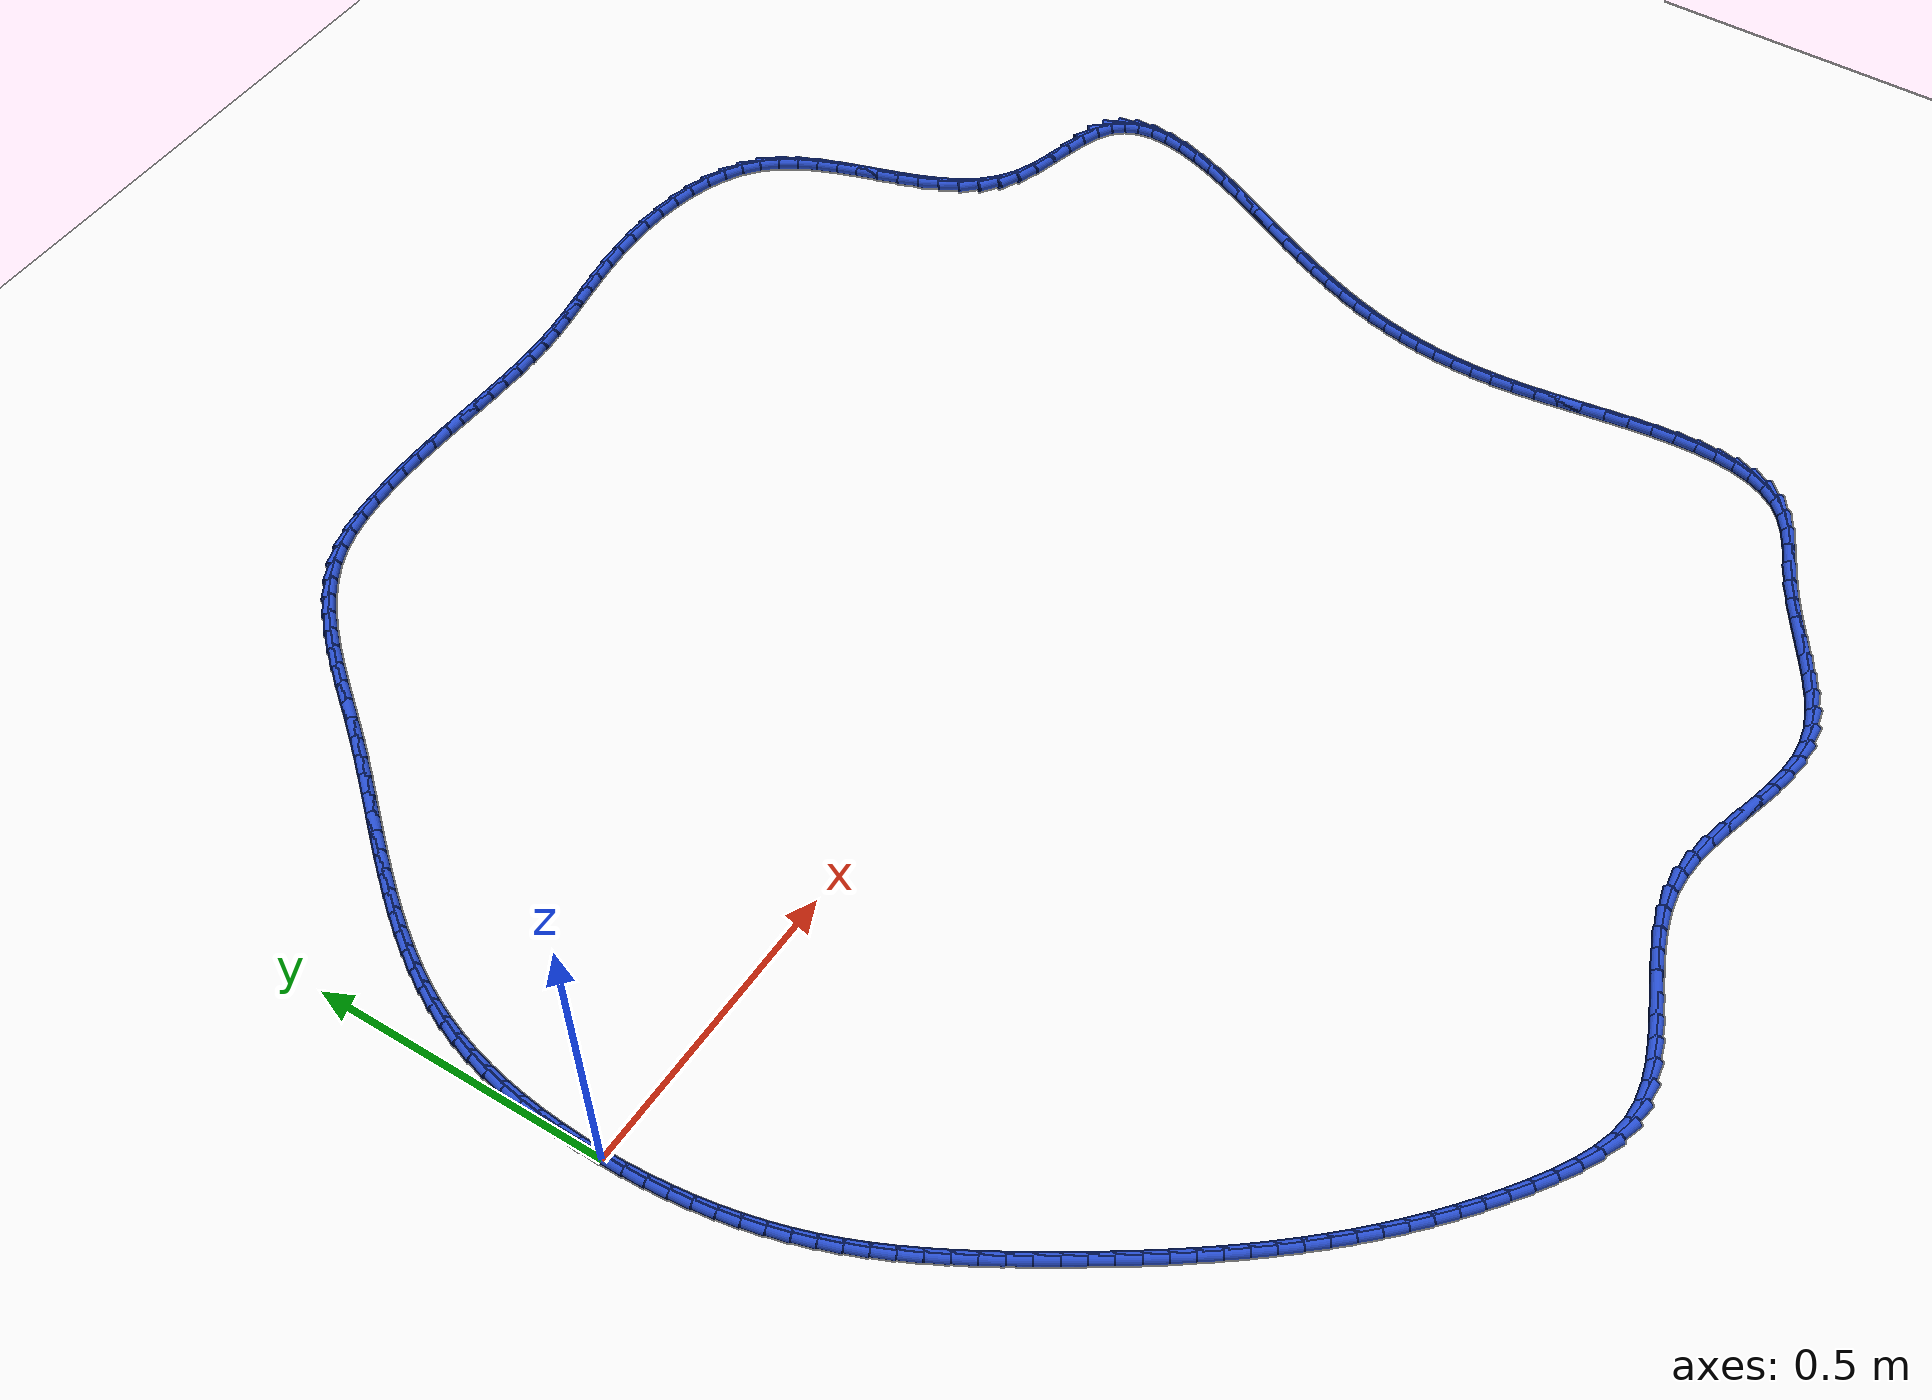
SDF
<sdf version="1.6">
 <world name="default">
  <light name="sun" type="directional">
   <pose>0 0 10 0 -0 0</pose>
   <diffuse>0.8 0.8 0.8 1</diffuse>
   <specular>0.2 0.2 0.2 1</specular>
   <attenuation>
    <range>1000</range>
    <constant>0.9</constant>
    <linear>0.01</linear>
    <quadratic>0.001</quadratic>
   </attenuation>
   <direction>-0.5 0.1 -0.9</direction>
  </light>
  <model name="ground_plane">
   <static>1</static>
   <link name="link">
    <collision name="collision">
     <geometry><plane><normal>0 0 1</normal><size>100 100</size></plane></geometry>
     <surface><friction><ode><mu>100</mu><mu2>50</mu2></ode></friction></surface>
    </collision>
    <visual name="visual">
     <cast_shadows>0</cast_shadows>
     <geometry><plane><normal>0 0 1</normal><size>100 100</size></plane></geometry>
     <material>
      <script><uri>file://media/materials/scripts/gazebo.material</uri><name>Gazebo/WhiteGlow</name></script>
     </material>
    </visual>
   </link>
  </model>
  <gravity>0 0 -9.8</gravity>
  <magnetic_field>6e-06 2.3e-05 -4.2e-05</magnetic_field>
  <atmosphere type="adiabatic"/>
  <physics name="default_physics" default="0" type="ode">
   <max_step_size>0.001</max_step_size>
   <real_time_factor>1</real_time_factor>
   <real_time_update_rate>1000</real_time_update_rate>
  </physics>
  <scene><ambient>0.4 0.4 0.4 1</ambient><background>0.7 0.7 0.7 1</background><shadows>1</shadows></scene>
  <spherical_coordinates>
   <surface_model>EARTH_WGS84</surface_model>
   <latitude_deg>0</latitude_deg>
   <longitude_deg>0</longitude_deg>
   <elevation>0</elevation>
   <heading_deg>0</heading_deg>
  </spherical_coordinates>
  <model name="line">
   <link name="link_0">
    <pose>-7.806255641895632e-18 -2.0816681711721685e-17 0.01 0 1.57 1.5617731594145254</pose>
    <collision name="collision">
     <geometry><cylinder><radius>0.01</radius><length>0.08</length></cylinder></geometry>
    </collision>
    <visual name="visual">
     <material>
      <script><name>Gazebo/Blue</name><uri>file://media/materials/scripts/gazebo.material</uri></script>
     </material>
     <geometry><cylinder><radius>0.01</radius><length>0.08</length></cylinder></geometry>
    </visual>
   </link>
   <link name="link_1">
    <pose>0.00032744630038928474 0.036288522634327094 0.01 0 1.57 1.5296438946750772</pose>
    <collision name="collision">
     <geometry><cylinder><radius>0.01</radius><length>0.08</length></cylinder></geometry>
    </collision>
    <visual name="visual">
     <material>
      <script><name>Gazebo/Blue</name><uri>file://media/materials/scripts/gazebo.material</uri></script>
     </material>
     <geometry><cylinder><radius>0.01</radius><length>0.08</length></cylinder></geometry>
    </visual>
   </link>
   <link name="link_2">
    <pose>0.0018213691328073014 0.07257020343789236 0.01 0 1.57 1.495147037033412</pose>
    <collision name="collision">
     <geometry><cylinder><radius>0.01</radius><length>0.08</length></cylinder></geometry>
    </collision>
    <visual name="visual">
     <material>
      <script><name>Gazebo/Blue</name><uri>file://media/materials/scripts/gazebo.material</uri></script>
     </material>
     <geometry><cylinder><radius>0.01</radius><length>0.08</length></cylinder></geometry>
    </visual>
   </link>
   <link name="link_3">
    <pose>0.004561372115958199 0.10872089504526695 0.01 0 1.57 1.4580126303335292</pose>
    <collision name="collision">
     <geometry><cylinder><radius>0.01</radius><length>0.08</length></cylinder></geometry>
    </collision>
    <visual name="visual">
     <material>
      <script><name>Gazebo/Blue</name><uri>file://media/materials/scripts/gazebo.material</uri></script>
     </material>
     <geometry><cylinder><radius>0.01</radius><length>0.08</length></cylinder></geometry>
    </visual>
   </link>
   <link name="link_4">
    <pose>0.008627058868546134 0.14461645009102214 0.01 0 1.57 1.417956326805844</pose>
    <collision name="collision">
     <geometry><cylinder><radius>0.01</radius><length>0.08</length></cylinder></geometry>
    </collision>
    <visual name="visual">
     <material>
      <script><name>Gazebo/Blue</name><uri>file://media/materials/scripts/gazebo.material</uri></script>
     </material>
     <geometry><cylinder><radius>0.01</radius><length>0.08</length></cylinder></geometry>
    </visual>
   </link>
   <link name="link_5">
    <pose>0.01409803300927527 0.18013272120972912 0.01 0 1.57 1.3746836692512767</pose>
    <collision name="collision">
     <geometry><cylinder><radius>0.01</radius><length>0.08</length></cylinder></geometry>
    </collision>
    <visual name="visual">
     <material>
      <script><name>Gazebo/Blue</name><uri>file://media/materials/scripts/gazebo.material</uri></script>
     </material>
     <geometry><cylinder><radius>0.01</radius><length>0.08</length></cylinder></geometry>
    </visual>
   </link>
   <link name="link_6">
    <pose>0.02105389815684977 0.21514556103595936 0.01 0 1.57 1.3278977589456853</pose>
    <collision name="collision">
     <geometry><cylinder><radius>0.01</radius><length>0.08</length></cylinder></geometry>
    </collision>
    <visual name="visual">
     <material>
      <script><name>Gazebo/Blue</name><uri>file://media/materials/scripts/gazebo.material</uri></script>
     </material>
     <geometry><cylinder><radius>0.01</radius><length>0.08</length></cylinder></geometry>
    </visual>
   </link>
   <link name="link_7">
    <pose>0.0295742579299738 0.24953082220428402 0.01 0 1.57 1.2773114094710651</pose>
    <collision name="collision">
     <geometry><cylinder><radius>0.01</radius><length>0.08</length></cylinder></geometry>
    </collision>
    <visual name="visual">
     <material>
      <script><name>Gazebo/Blue</name><uri>file://media/materials/scripts/gazebo.material</uri></script>
     </material>
     <geometry><cylinder><radius>0.01</radius><length>0.08</length></cylinder></geometry>
    </visual>
   </link>
   <link name="link_8">
    <pose>0.039738715947351504 0.28316435734927425 0.01 0 1.57 1.2226780229586476</pose>
    <collision name="collision">
     <geometry><cylinder><radius>0.01</radius><length>0.08</length></cylinder></geometry>
    </collision>
    <visual name="visual">
     <material>
      <script><name>Gazebo/Blue</name><uri>file://media/materials/scripts/gazebo.material</uri></script>
     </material>
     <geometry><cylinder><radius>0.01</radius><length>0.08</length></cylinder></geometry>
    </visual>
   </link>
   <link name="link_9">
    <pose>0.05162652246071975 0.3159223826145671 0.01 0 1.57 1.1662294091827403</pose>
    <collision name="collision">
     <geometry><cylinder><radius>0.01</radius><length>0.08</length></cylinder></geometry>
    </collision>
    <visual name="visual">
     <material>
      <script><name>Gazebo/Blue</name><uri>file://media/materials/scripts/gazebo.material</uri></script>
     </material>
     <geometry><cylinder><radius>0.01</radius><length>0.08</length></cylinder></geometry>
    </visual>
   </link>
   <link name="link_10">
    <pose>0.06525324665883812 0.34774662293733566 0.01 0 1.57 1.113424842363254</pose>
    <collision name="collision">
     <geometry><cylinder><radius>0.01</radius><length>0.08</length></cylinder></geometry>
    </collision>
    <visual name="visual">
     <material>
      <script><name>Gazebo/Blue</name><uri>file://media/materials/scripts/gazebo.material</uri></script>
     </material>
     <geometry><cylinder><radius>0.01</radius><length>0.08</length></cylinder></geometry>
    </visual>
   </link>
   <link name="link_11">
    <pose>0.08049753287873879 0.37871965803044927 0.01 0 1.57 1.0654095106883927</pose>
    <collision name="collision">
     <geometry><cylinder><radius>0.01</radius><length>0.08</length></cylinder></geometry>
    </collision>
    <visual name="visual">
     <material>
      <script><name>Gazebo/Blue</name><uri>file://media/materials/scripts/gazebo.material</uri></script>
     </material>
     <geometry><cylinder><radius>0.01</radius><length>0.08</length></cylinder></geometry>
    </visual>
   </link>
   <link name="link_12">
    <pose>0.09722027224663352 0.4089423303581806 0.01 0 1.57 1.0225029665042582</pose>
    <collision name="collision">
     <geometry><cylinder><radius>0.01</radius><length>0.08</length></cylinder></geometry>
    </collision>
    <visual name="visual">
     <material>
      <script><name>Gazebo/Blue</name><uri>file://media/materials/scripts/gazebo.material</uri></script>
     </material>
     <geometry><cylinder><radius>0.01</radius><length>0.08</length></cylinder></geometry>
    </visual>
   </link>
   <link name="link_13">
    <pose>0.11528235588873408 0.4385154823848024 0.01 0 1.57 0.9848796700418869</pose>
    <collision name="collision">
     <geometry><cylinder><radius>0.01</radius><length>0.08</length></cylinder></geometry>
    </collision>
    <visual name="visual">
     <material>
      <script><name>Gazebo/Blue</name><uri>file://media/materials/scripts/gazebo.material</uri></script>
     </material>
     <geometry><cylinder><radius>0.01</radius><length>0.08</length></cylinder></geometry>
    </visual>
   </link>
   <link name="link_14">
    <pose>0.13454467493125222 0.46753995657458697 0.01 0 1.57 0.952599108806189</pose>
    <collision name="collision">
     <geometry><cylinder><radius>0.01</radius><length>0.08</length></cylinder></geometry>
    </collision>
    <visual name="visual">
     <material>
      <script><name>Gazebo/Blue</name><uri>file://media/materials/scripts/gazebo.material</uri></script>
     </material>
     <geometry><cylinder><radius>0.01</radius><length>0.08</length></cylinder></geometry>
    </visual>
   </link>
   <link name="link_15">
    <pose>0.1548681205003997 0.49611659539180686 0.01 0 1.57 0.9256370994258802</pose>
    <collision name="collision">
     <geometry><cylinder><radius>0.01</radius><length>0.08</length></cylinder></geometry>
    </collision>
    <visual name="visual">
     <material>
      <script><name>Gazebo/Blue</name><uri>file://media/materials/scripts/gazebo.material</uri></script>
     </material>
     <geometry><cylinder><radius>0.01</radius><length>0.08</length></cylinder></geometry>
    </visual>
   </link>
   <link name="link_16">
    <pose>0.17611358372238828 0.524346241300735 0.01 0 1.57 0.9039143389724964</pose>
    <collision name="collision">
     <geometry><cylinder><radius>0.01</radius><length>0.08</length></cylinder></geometry>
    </collision>
    <visual name="visual">
     <material>
      <script><name>Gazebo/Blue</name><uri>file://media/materials/scripts/gazebo.material</uri></script>
     </material>
     <geometry><cylinder><radius>0.01</radius><length>0.08</length></cylinder></geometry>
    </visual>
   </link>
   <link name="link_17">
    <pose>0.1981419557234298 0.5523297367656436 0.01 0 1.57 0.8873201236100704</pose>
    <collision name="collision">
     <geometry><cylinder><radius>0.01</radius><length>0.08</length></cylinder></geometry>
    </collision>
    <visual name="visual">
     <material>
      <script><name>Gazebo/Blue</name><uri>file://media/materials/scripts/gazebo.material</uri></script>
     </material>
     <geometry><cylinder><radius>0.01</radius><length>0.08</length></cylinder></geometry>
    </visual>
   </link>
   <link name="link_18">
    <pose>0.22081412762973585 0.5801679242508053 0.01 0 1.57 0.8757305470665164</pose>
    <collision name="collision">
     <geometry><cylinder><radius>0.01</radius><length>0.08</length></cylinder></geometry>
    </collision>
    <visual name="visual">
     <material>
      <script><name>Gazebo/Blue</name><uri>file://media/materials/scripts/gazebo.material</uri></script>
     </material>
     <geometry><cylinder><radius>0.01</radius><length>0.08</length></cylinder></geometry>
    </visual>
   </link>
   <link name="link_19">
    <pose>0.24399099056751844 0.607961646220493 0.01 0 1.57 0.8690213487096884</pose>
    <collision name="collision">
     <geometry><cylinder><radius>0.01</radius><length>0.08</length></cylinder></geometry>
    </collision>
    <visual name="visual">
     <material>
      <script><name>Gazebo/Blue</name><uri>file://media/materials/scripts/gazebo.material</uri></script>
     </material>
     <geometry><cylinder><radius>0.01</radius><length>0.08</length></cylinder></geometry>
    </visual>
   </link>
   <link name="link_20">
    <pose>0.26753343566298915 0.6358117451389789 0.01 0 1.57 0.8670759920582112</pose>
    <collision name="collision">
     <geometry><cylinder><radius>0.01</radius><length>0.08</length></cylinder></geometry>
    </collision>
    <visual name="visual">
     <material>
      <script><name>Gazebo/Blue</name><uri>file://media/materials/scripts/gazebo.material</uri></script>
     </material>
     <geometry><cylinder><radius>0.01</radius><length>0.08</length></cylinder></geometry>
    </visual>
   </link>
   <link name="link_21">
    <pose>0.2913023540423597 0.6638190634705357 0.01 0 1.57 0.8697896640838979</pose>
    <collision name="collision">
     <geometry><cylinder><radius>0.01</radius><length>0.08</length></cylinder></geometry>
    </collision>
    <visual name="visual">
     <material>
      <script><name>Gazebo/Blue</name><uri>file://media/materials/scripts/gazebo.material</uri></script>
     </material>
     <geometry><cylinder><radius>0.01</radius><length>0.08</length></cylinder></geometry>
    </visual>
   </link>
   <link name="link_22">
    <pose>0.3151586368318421 0.692084443679436 0.01 0 1.57 0.8770698273195979</pose>
    <collision name="collision">
     <geometry><cylinder><radius>0.01</radius><length>0.08</length></cylinder></geometry>
    </collision>
    <visual name="visual">
     <material>
      <script><name>Gazebo/Blue</name><uri>file://media/materials/scripts/gazebo.material</uri></script>
     </material>
     <geometry><cylinder><radius>0.01</radius><length>0.08</length></cylinder></geometry>
    </visual>
   </link>
   <link name="link_23">
    <pose>0.33896317515764784 0.7207087282299524 0.01 0 1.57 0.8888338310618514</pose>
    <collision name="collision">
     <geometry><cylinder><radius>0.01</radius><length>0.08</length></cylinder></geometry>
    </collision>
    <visual name="visual">
     <material>
      <script><name>Gazebo/Blue</name><uri>file://media/materials/scripts/gazebo.material</uri></script>
     </material>
     <geometry><cylinder><radius>0.01</radius><length>0.08</length></cylinder></geometry>
    </visual>
   </link>
   <link name="link_24">
    <pose>0.3625768601459888 0.7497927595863572 0.01 0 1.57 0.9043316246221482</pose>
    <collision name="collision">
     <geometry><cylinder><radius>0.01</radius><length>0.08</length></cylinder></geometry>
    </collision>
    <visual name="visual">
     <material>
      <script><name>Gazebo/Blue</name><uri>file://media/materials/scripts/gazebo.material</uri></script>
     </material>
     <geometry><cylinder><radius>0.01</radius><length>0.08</length></cylinder></geometry>
    </visual>
   </link>
   <link name="link_25">
    <pose>0.3858759281696378 0.7794158949197898 0.01 0 1.57 0.9146816644497419</pose>
    <collision name="collision">
     <geometry><cylinder><radius>0.01</radius><length>0.08</length></cylinder></geometry>
    </collision>
    <visual name="visual">
     <material>
      <script><name>Gazebo/Blue</name><uri>file://media/materials/scripts/gazebo.material</uri></script>
     </material>
     <geometry><cylinder><radius>0.01</radius><length>0.08</length></cylinder></geometry>
    </visual>
   </link>
   <link name="link_26">
    <pose>0.4089398232527042 0.8093729748940368 0.01 0 1.57 0.9137533687731932</pose>
    <collision name="collision">
     <geometry><cylinder><radius>0.01</radius><length>0.08</length></cylinder></geometry>
    </collision>
    <visual name="visual">
     <material>
      <script><name>Gazebo/Blue</name><uri>file://media/materials/scripts/gazebo.material</uri></script>
     </material>
     <geometry><cylinder><radius>0.01</radius><length>0.08</length></cylinder></geometry>
    </visual>
   </link>
   <link name="link_27">
    <pose>0.43199192764884187 0.8392573083797915 0.01 0 1.57 0.9013404433406285</pose>
    <collision name="collision">
     <geometry><cylinder><radius>0.01</radius><length>0.08</length></cylinder></geometry>
    </collision>
    <visual name="visual">
     <material>
      <script><name>Gazebo/Blue</name><uri>file://media/materials/scripts/gazebo.material</uri></script>
     </material>
     <geometry><cylinder><radius>0.01</radius><length>0.08</length></cylinder></geometry>
    </visual>
   </link>
   <link name="link_28">
    <pose>0.4552586713110886 0.8686579370817289 0.01 0 1.57 0.8770351752608088</pose>
    <collision name="collision">
     <geometry><cylinder><radius>0.01</radius><length>0.08</length></cylinder></geometry>
    </collision>
    <visual name="visual">
     <material>
      <script><name>Gazebo/Blue</name><uri>file://media/materials/scripts/gazebo.material</uri></script>
     </material>
     <geometry><cylinder><radius>0.01</radius><length>0.08</length></cylinder></geometry>
    </visual>
   </link>
   <link name="link_29">
    <pose>0.47896648419248233 0.8971639027045247 0.01 0 1.57 0.8401180100385603</pose>
    <collision name="collision">
     <geometry><cylinder><radius>0.01</radius><length>0.08</length></cylinder></geometry>
    </collision>
    <visual name="visual">
     <material>
      <script><name>Gazebo/Blue</name><uri>file://media/materials/scripts/gazebo.material</uri></script>
     </material>
     <geometry><cylinder><radius>0.01</radius><length>0.08</length></cylinder></geometry>
    </visual>
   </link>
   <link name="link_30">
    <pose>0.5033417962460612 0.924364246952855 0.01 0 1.57 0.7896249499492259</pose>
    <collision name="collision">
     <geometry><cylinder><radius>0.01</radius><length>0.08</length></cylinder></geometry>
    </collision>
    <visual name="visual">
     <material>
      <script><name>Gazebo/Blue</name><uri>file://media/materials/scripts/gazebo.material</uri></script>
     </material>
     <geometry><cylinder><radius>0.01</radius><length>0.08</length></cylinder></geometry>
    </visual>
   </link>
   <link name="link_31">
    <pose>0.5286110374248632 0.9498480115313945 0.01 0 1.57 0.7244961222345467</pose>
    <collision name="collision">
     <geometry><cylinder><radius>0.01</radius><length>0.08</length></cylinder></geometry>
    </collision>
    <visual name="visual">
     <material>
      <script><name>Gazebo/Blue</name><uri>file://media/materials/scripts/gazebo.material</uri></script>
     </material>
     <geometry><cylinder><radius>0.01</radius><length>0.08</length></cylinder></geometry>
    </visual>
   </link>
   <link name="link_32">
    <pose>0.5550006376819262 0.973204238144819 0.01 0 1.57 0.6438572448374091</pose>
    <collision name="collision">
     <geometry><cylinder><radius>0.01</radius><length>0.08</length></cylinder></geometry>
    </collision>
    <visual name="visual">
     <material>
      <script><name>Gazebo/Blue</name><uri>file://media/materials/scripts/gazebo.material</uri></script>
     </material>
     <geometry><cylinder><radius>0.01</radius><length>0.08</length></cylinder></geometry>
    </visual>
   </link>
   <link name="link_33">
    <pose>0.5827370269702883 0.9940219684978044 0.01 0 1.57 0.547476759684378</pose>
    <collision name="collision">
     <geometry><cylinder><radius>0.01</radius><length>0.08</length></cylinder></geometry>
    </collision>
    <visual name="visual">
     <material>
      <script><name>Gazebo/Blue</name><uri>file://media/materials/scripts/gazebo.material</uri></script>
     </material>
     <geometry><cylinder><radius>0.01</radius><length>0.08</length></cylinder></geometry>
    </visual>
   </link>
   <link name="link_34">
    <pose>0.6120466352429873 1.0118902442950257 0.01 0 1.57 0.43636869826445623</pose>
    <collision name="collision">
     <geometry><cylinder><radius>0.01</radius><length>0.08</length></cylinder></geometry>
    </collision>
    <visual name="visual">
     <material>
      <script><name>Gazebo/Blue</name><uri>file://media/materials/scripts/gazebo.material</uri></script>
     </material>
     <geometry><cylinder><radius>0.01</radius><length>0.08</length></cylinder></geometry>
    </visual>
   </link>
   <link name="link_35">
    <pose>0.6431558924530612 1.0263981072411583 0.01 0 1.57 0.3146501721234525</pose>
    <collision name="collision">
     <geometry><cylinder><radius>0.01</radius><length>0.08</length></cylinder></geometry>
    </collision>
    <visual name="visual">
     <material>
      <script><name>Gazebo/Blue</name><uri>file://media/materials/scripts/gazebo.material</uri></script>
     </material>
     <geometry><cylinder><radius>0.01</radius><length>0.08</length></cylinder></geometry>
    </visual>
   </link>
   <link name="link_36">
    <pose>0.6762613386042085 1.037172689039796 0.01 0 1.57 0.20700200496431614</pose>
    <collision name="collision">
     <geometry><cylinder><radius>0.01</radius><length>0.08</length></cylinder></geometry>
    </collision>
    <visual name="visual">
     <material>
      <script><name>Gazebo/Blue</name><uri>file://media/materials/scripts/gazebo.material</uri></script>
     </material>
     <geometry><cylinder><radius>0.01</radius><length>0.08</length></cylinder></geometry>
    </visual>
   </link>
   <link name="link_37">
    <pose>0.7110579169194895 1.0444803269219516 0.01 0 1.57 0.12892980339322338</pose>
    <collision name="collision">
     <geometry><cylinder><radius>0.01</radius><length>0.08</length></cylinder></geometry>
    </collision>
    <visual name="visual">
     <material>
      <script><name>Gazebo/Blue</name><uri>file://media/materials/scripts/gazebo.material</uri></script>
     </material>
     <geometry><cylinder><radius>0.01</radius><length>0.08</length></cylinder></geometry>
    </visual>
   </link>
   <link name="link_38">
    <pose>0.746824604092575 1.04911744147457 0.01 0 1.57 0.07601861250404313</pose>
    <collision name="collision">
     <geometry><cylinder><radius>0.01</radius><length>0.08</length></cylinder></geometry>
    </collision>
    <visual name="visual">
     <material>
      <script><name>Gazebo/Blue</name><uri>file://media/materials/scripts/gazebo.material</uri></script>
     </material>
     <geometry><cylinder><radius>0.01</radius><length>0.08</length></cylinder></geometry>
    </visual>
   </link>
   <link name="link_39">
    <pose>0.7828713051989048 1.0518629523296015 0.01 0 1.57 0.036199277869939206</pose>
    <collision name="collision">
     <geometry><cylinder><radius>0.01</radius><length>0.08</length></cylinder></geometry>
    </collision>
    <visual name="visual">
     <material>
      <script><name>Gazebo/Blue</name><uri>file://media/materials/scripts/gazebo.material</uri></script>
     </material>
     <geometry><cylinder><radius>0.01</radius><length>0.08</length></cylinder></geometry>
    </visual>
   </link>
   <link name="link_40">
    <pose>0.8189320868947491 1.0531688970675703 0.01 0 1.57 0.003716762033867465</pose>
    <collision name="collision">
     <geometry><cylinder><radius>0.01</radius><length>0.08</length></cylinder></geometry>
    </collision>
    <visual name="visual">
     <material>
      <script><name>Gazebo/Blue</name><uri>file://media/materials/scripts/gazebo.material</uri></script>
     </material>
     <geometry><cylinder><radius>0.01</radius><length>0.08</length></cylinder></geometry>
    </visual>
   </link>
   <link name="link_41">
    <pose>0.8549803355457485 1.0533028804465074 0.01 0 1.57 -0.021446642383102763</pose>
    <collision name="collision">
     <geometry><cylinder><radius>0.01</radius><length>0.08</length></cylinder></geometry>
    </collision>
    <visual name="visual">
     <material>
      <script><name>Gazebo/Blue</name><uri>file://media/materials/scripts/gazebo.material</uri></script>
     </material>
     <geometry><cylinder><radius>0.01</radius><length>0.08</length></cylinder></geometry>
    </visual>
   </link>
   <link name="link_42">
    <pose>0.8909921330921732 1.0525304298675962 0.01 0 1.57 -0.03929272785194849</pose>
    <collision name="collision">
     <geometry><cylinder><radius>0.01</radius><length>0.08</length></cylinder></geometry>
    </collision>
    <visual name="visual">
     <material>
      <script><name>Gazebo/Blue</name><uri>file://media/materials/scripts/gazebo.material</uri></script>
     </material>
     <geometry><cylinder><radius>0.01</radius><length>0.08</length></cylinder></geometry>
    </visual>
   </link>
   <link name="link_43">
    <pose>0.9269435614742935 1.0511170727320194 0.01 0 1.57 -0.04982988608390382</pose>
    <collision name="collision">
     <geometry><cylinder><radius>0.01</radius><length>0.08</length></cylinder></geometry>
    </collision>
    <visual name="visual">
     <material>
      <script><name>Gazebo/Blue</name><uri>file://media/materials/scripts/gazebo.material</uri></script>
     </material>
     <geometry><cylinder><radius>0.01</radius><length>0.08</length></cylinder></geometry>
    </visual>
   </link>
   <link name="link_44">
    <pose>0.9628107026323792 1.049328336440961 0.01 0 1.57 -0.05304428059340749</pose>
    <collision name="collision">
     <geometry><cylinder><radius>0.01</radius><length>0.08</length></cylinder></geometry>
    </collision>
    <visual name="visual">
     <material>
      <script><name>Gazebo/Blue</name><uri>file://media/materials/scripts/gazebo.material</uri></script>
     </material>
     <geometry><cylinder><radius>0.01</radius><length>0.08</length></cylinder></geometry>
    </visual>
   </link>
   <link name="link_45">
    <pose>0.9985696385067008 1.0474297483956034 0.01 0 1.57 -0.04888239588245125</pose>
    <collision name="collision">
     <geometry><cylinder><radius>0.01</radius><length>0.08</length></cylinder></geometry>
    </collision>
    <visual name="visual">
     <material>
      <script><name>Gazebo/Blue</name><uri>file://media/materials/scripts/gazebo.material</uri></script>
     </material>
     <geometry><cylinder><radius>0.01</radius><length>0.08</length></cylinder></geometry>
    </visual>
   </link>
   <link name="link_46">
    <pose>1.034196451037528 1.0456868359971303 0.01 0 1.57 -0.03724469775519393</pose>
    <collision name="collision">
     <geometry><cylinder><radius>0.01</radius><length>0.08</length></cylinder></geometry>
    </collision>
    <visual name="visual">
     <material>
      <script><name>Gazebo/Blue</name><uri>file://media/materials/scripts/gazebo.material</uri></script>
     </material>
     <geometry><cylinder><radius>0.01</radius><length>0.08</length></cylinder></geometry>
    </visual>
   </link>
   <link name="link_47">
    <pose>1.0696672221651309 1.0443651266467244 0.01 0 1.57 -0.01799081296213666</pose>
    <collision name="collision">
     <geometry><cylinder><radius>0.01</radius><length>0.08</length></cylinder></geometry>
    </collision>
    <visual name="visual">
     <material>
      <script><name>Gazebo/Blue</name><uri>file://media/materials/scripts/gazebo.material</uri></script>
     </material>
     <geometry><cylinder><radius>0.01</radius><length>0.08</length></cylinder></geometry>
    </visual>
   </link>
   <link name="link_48">
    <pose>1.1049580338297793 1.0437301477455692 0.01 0 1.57 0.009042405942307612</pose>
    <collision name="collision">
     <geometry><cylinder><radius>0.01</radius><length>0.08</length></cylinder></geometry>
    </collision>
    <visual name="visual">
     <material>
      <script><name>Gazebo/Blue</name><uri>file://media/materials/scripts/gazebo.material</uri></script>
     </material>
     <geometry><cylinder><radius>0.01</radius><length>0.08</length></cylinder></geometry>
    </visual>
   </link>
   <link name="link_49">
    <pose>1.1400449679717441 1.0440474266948478 0.01 0 1.57 0.04400777409112347</pose>
    <collision name="collision">
     <geometry><cylinder><radius>0.01</radius><length>0.08</length></cylinder></geometry>
    </collision>
    <visual name="visual">
     <material>
      <script><name>Gazebo/Blue</name><uri>file://media/materials/scripts/gazebo.material</uri></script>
     </material>
     <geometry><cylinder><radius>0.01</radius><length>0.08</length></cylinder></geometry>
    </visual>
   </link>
   <link name="link_50">
    <pose>1.1749041065312948 1.0455824908957434 0.01 0 1.57 0.08690252325414222</pose>
    <collision name="collision">
     <geometry><cylinder><radius>0.01</radius><length>0.08</length></cylinder></geometry>
    </collision>
    <visual name="visual">
     <material>
      <script><name>Gazebo/Blue</name><uri>file://media/materials/scripts/gazebo.material</uri></script>
     </material>
     <geometry><cylinder><radius>0.01</radius><length>0.08</length></cylinder></geometry>
    </visual>
   </link>
   <link name="link_51">
    <pose>1.209512626546147 1.0485976526513074 0.01 0 1.57 0.12944948917517576</pose>
    <collision name="collision">
     <geometry><cylinder><radius>0.01</radius><length>0.08</length></cylinder></geometry>
    </collision>
    <visual name="visual">
     <material>
      <script><name>Gazebo/Blue</name><uri>file://media/materials/scripts/gazebo.material</uri></script>
     </material>
     <geometry><cylinder><radius>0.01</radius><length>0.08</length></cylinder></geometry>
    </visual>
   </link>
   <link name="link_52">
    <pose>1.2439416097041491 1.0530795294701196 0.01 0 1.57 0.1567974519001596</pose>
    <collision name="collision">
     <geometry><cylinder><radius>0.01</radius><length>0.08</length></cylinder></geometry>
    </collision>
    <visual name="visual">
     <material>
      <script><name>Gazebo/Blue</name><uri>file://media/materials/scripts/gazebo.material</uri></script>
     </material>
     <geometry><cylinder><radius>0.01</radius><length>0.08</length></cylinder></geometry>
    </visual>
   </link>
   <link name="link_53">
    <pose>1.2784267464284507 1.0585314638431451 0.01 0 1.57 0.16731564833161217</pose>
    <collision name="collision">
     <geometry><cylinder><radius>0.01</radius><length>0.08</length></cylinder></geometry>
    </collision>
    <visual name="visual">
     <material>
      <script><name>Gazebo/Blue</name><uri>file://media/materials/scripts/gazebo.material</uri></script>
     </material>
     <geometry><cylinder><radius>0.01</radius><length>0.08</length></cylinder></geometry>
    </visual>
   </link>
   <link name="link_54">
    <pose>1.313220375192999 1.0644079212255768 0.01 0 1.57 0.16137700495100282</pose>
    <collision name="collision">
     <geometry><cylinder><radius>0.01</radius><length>0.08</length></cylinder></geometry>
    </collision>
    <visual name="visual">
     <material>
      <script><name>Gazebo/Blue</name><uri>file://media/materials/scripts/gazebo.material</uri></script>
     </material>
     <geometry><cylinder><radius>0.01</radius><length>0.08</length></cylinder></geometry>
    </visual>
   </link>
   <link name="link_55">
    <pose>1.3485748344717436 1.0701633670726083 0.01 0 1.57 0.13978552267074787</pose>
    <collision name="collision">
     <geometry><cylinder><radius>0.01</radius><length>0.08</length></cylinder></geometry>
    </collision>
    <visual name="visual">
     <material>
      <script><name>Gazebo/Blue</name><uri>file://media/materials/scripts/gazebo.material</uri></script>
     </material>
     <geometry><cylinder><radius>0.01</radius><length>0.08</length></cylinder></geometry>
    </visual>
   </link>
   <link name="link_56">
    <pose>1.384742462738633 1.0752522668394329 0.01 0 1.57 0.1038141333362771</pose>
    <collision name="collision">
     <geometry><cylinder><radius>0.01</radius><length>0.08</length></cylinder></geometry>
    </collision>
    <visual name="visual">
     <material>
      <script><name>Gazebo/Blue</name><uri>file://media/materials/scripts/gazebo.material</uri></script>
     </material>
     <geometry><cylinder><radius>0.01</radius><length>0.08</length></cylinder></geometry>
    </visual>
   </link>
   <link name="link_57">
    <pose>1.4219698863697836 1.0791309435653766 0.01 0 1.57 0.05814658154505345</pose>
    <collision name="collision">
     <geometry><cylinder><radius>0.01</radius><length>0.08</length></cylinder></geometry>
    </collision>
    <visual name="visual">
     <material>
      <script><name>Gazebo/Blue</name><uri>file://media/materials/scripts/gazebo.material</uri></script>
     </material>
     <geometry><cylinder><radius>0.01</radius><length>0.08</length></cylinder></geometry>
    </visual>
   </link>
   <link name="link_58">
    <pose>1.4601950229192853 1.0813561129346456 0.01 0 1.57 0.007181583870500219</pose>
    <collision name="collision">
     <geometry><cylinder><radius>0.01</radius><length>0.08</length></cylinder></geometry>
    </collision>
    <visual name="visual">
     <material>
      <script><name>Gazebo/Blue</name><uri>file://media/materials/scripts/gazebo.material</uri></script>
     </material>
     <geometry><cylinder><radius>0.01</radius><length>0.08</length></cylinder></geometry>
    </visual>
   </link>
   <link name="link_59">
    <pose>1.4988958889622865 1.081634051228247 0.01 0 1.57 -0.05047436283816066</pose>
    <collision name="collision">
     <geometry><cylinder><radius>0.01</radius><length>0.08</length></cylinder></geometry>
    </collision>
    <visual name="visual">
     <material>
      <script><name>Gazebo/Blue</name><uri>file://media/materials/scripts/gazebo.material</uri></script>
     </material>
     <geometry><cylinder><radius>0.01</radius><length>0.08</length></cylinder></geometry>
    </visual>
   </link>
   <link name="link_60">
    <pose>1.5375130362401277 1.0796832183561842 0.01 0 1.57 -0.11694294829557393</pose>
    <collision name="collision">
     <geometry><cylinder><radius>0.01</radius><length>0.08</length></cylinder></geometry>
    </collision>
    <visual name="visual">
     <material>
      <script><name>Gazebo/Blue</name><uri>file://media/materials/scripts/gazebo.material</uri></script>
     </material>
     <geometry><cylinder><radius>0.01</radius><length>0.08</length></cylinder></geometry>
    </visual>
   </link>
   <link name="link_61">
    <pose>1.5754870164941495 1.075222074228462 0.01 0 1.57 -0.19474584557214875</pose>
    <collision name="collision">
     <geometry><cylinder><radius>0.01</radius><length>0.08</length></cylinder></geometry>
    </collision>
    <visual name="visual">
     <material>
      <script><name>Gazebo/Blue</name><uri>file://media/materials/scripts/gazebo.material</uri></script>
     </material>
     <geometry><cylinder><radius>0.01</radius><length>0.08</length></cylinder></geometry>
    </visual>
   </link>
   <link name="link_62">
    <pose>1.6122583814656928 1.0679690787550853 0.01 0 1.57 -0.2868276908165692</pose>
    <collision name="collision">
     <geometry><cylinder><radius>0.01</radius><length>0.08</length></cylinder></geometry>
    </collision>
    <visual name="visual">
     <material>
      <script><name>Gazebo/Blue</name><uri>file://media/materials/scripts/gazebo.material</uri></script>
     </material>
     <geometry><cylinder><radius>0.01</radius><length>0.08</length></cylinder></geometry>
    </visual>
   </link>
   <link name="link_63">
    <pose>1.6472676828960986 1.0576426918460577 0.01 0 1.57 -0.3963907209809549</pose>
    <collision name="collision">
     <geometry><cylinder><radius>0.01</radius><length>0.08</length></cylinder></geometry>
    </collision>
    <visual name="visual">
     <material>
      <script><name>Gazebo/Blue</name><uri>file://media/materials/scripts/gazebo.material</uri></script>
     </material>
     <geometry><cylinder><radius>0.01</radius><length>0.08</length></cylinder></geometry>
    </visual>
   </link>
   <link name="link_64">
    <pose>1.6799554725267076 1.0439613734113842 0.01 0 1.57 -0.5263323012996315</pose>
    <collision name="collision">
     <geometry><cylinder><radius>0.01</radius><length>0.08</length></cylinder></geometry>
    </collision>
    <visual name="visual">
     <material>
      <script><name>Gazebo/Blue</name><uri>file://media/materials/scripts/gazebo.material</uri></script>
     </material>
     <geometry><cylinder><radius>0.01</radius><length>0.08</length></cylinder></geometry>
    </visual>
   </link>
   <link name="link_65">
    <pose>1.70976230209886 1.0266435833610683 0.01 0 1.57 -0.6780315437875424</pose>
    <collision name="collision">
     <geometry><cylinder><radius>0.01</radius><length>0.08</length></cylinder></geometry>
    </collision>
    <visual name="visual">
     <material>
      <script><name>Gazebo/Blue</name><uri>file://media/materials/scripts/gazebo.material</uri></script>
     </material>
     <geometry><cylinder><radius>0.01</radius><length>0.08</length></cylinder></geometry>
    </visual>
   </link>
   <link name="link_66">
    <pose>1.7361287233538978 1.005407781605115 0.01 0 1.57 -0.8470419272122244</pose>
    <collision name="collision">
     <geometry><cylinder><radius>0.01</radius><length>0.08</length></cylinder></geometry>
    </collision>
    <visual name="visual">
     <material>
      <script><name>Gazebo/Blue</name><uri>file://media/materials/scripts/gazebo.material</uri></script>
     </material>
     <geometry><cylinder><radius>0.01</radius><length>0.08</length></cylinder></geometry>
    </visual>
   </link>
   <link name="link_67">
    <pose>1.7585607022753573 0.9800245542515559 0.01 0 1.57 -0.9990008211919433</pose>
    <collision name="collision">
     <geometry><cylinder><radius>0.01</radius><length>0.08</length></cylinder></geometry>
    </collision>
    <visual name="visual">
     <material>
      <script><name>Gazebo/Blue</name><uri>file://media/materials/scripts/gazebo.material</uri></script>
     </material>
     <geometry><cylinder><radius>0.01</radius><length>0.08</length></cylinder></geometry>
    </visual>
   </link>
   <link name="link_68">
    <pose>1.7773225668048496 0.9508687980948362 0.01 0 1.57 -1.1130805498657297</pose>
    <collision name="collision">
     <geometry><cylinder><radius>0.01</radius><length>0.08</length></cylinder></geometry>
    </collision>
    <visual name="visual">
     <material>
      <script><name>Gazebo/Blue</name><uri>file://media/materials/scripts/gazebo.material</uri></script>
     </material>
     <geometry><cylinder><radius>0.01</radius><length>0.08</length></cylinder></geometry>
    </visual>
   </link>
   <link name="link_69">
    <pose>1.7931669254652318 0.9187045027235152 0.01 0 1.57 -1.1921306621814383</pose>
    <collision name="collision">
     <geometry><cylinder><radius>0.01</radius><length>0.08</length></cylinder></geometry>
    </collision>
    <visual name="visual">
     <material>
      <script><name>Gazebo/Blue</name><uri>file://media/materials/scripts/gazebo.material</uri></script>
     </material>
     <geometry><cylinder><radius>0.01</radius><length>0.08</length></cylinder></geometry>
    </visual>
   </link>
   <link name="link_70">
    <pose>1.8068544806407896 0.8843021074259336 0.01 0 1.57 -1.2406698823326725</pose>
    <collision name="collision">
     <geometry><cylinder><radius>0.01</radius><length>0.08</length></cylinder></geometry>
    </collision>
    <visual name="visual">
     <material>
      <script><name>Gazebo/Blue</name><uri>file://media/materials/scripts/gazebo.material</uri></script>
     </material>
     <geometry><cylinder><radius>0.01</radius><length>0.08</length></cylinder></geometry>
    </visual>
   </link>
   <link name="link_71">
    <pose>1.8191459347158088 0.848432051490432 0.01 0 1.57 -1.2622218312819644</pose>
    <collision name="collision">
     <geometry><cylinder><radius>0.01</radius><length>0.08</length></cylinder></geometry>
    </collision>
    <visual name="visual">
     <material>
      <script><name>Gazebo/Blue</name><uri>file://media/materials/scripts/gazebo.material</uri></script>
     </material>
     <geometry><cylinder><radius>0.01</radius><length>0.08</length></cylinder></geometry>
    </visual>
   </link>
   <link name="link_72">
    <pose>1.8308019900745742 0.8118647742053492 0.01 0 1.57 -1.2585288191707322</pose>
    <collision name="collision">
     <geometry><cylinder><radius>0.01</radius><length>0.08</length></cylinder></geometry>
    </collision>
    <visual name="visual">
     <material>
      <script><name>Gazebo/Blue</name><uri>file://media/materials/scripts/gazebo.material</uri></script>
     </material>
     <geometry><cylinder><radius>0.01</radius><length>0.08</length></cylinder></geometry>
    </visual>
   </link>
   <link name="link_73">
    <pose>1.8425833491013708 0.7753707148590262 0.01 0 1.57 -1.2293883715992928</pose>
    <collision name="collision">
     <geometry><cylinder><radius>0.01</radius><length>0.08</length></cylinder></geometry>
    </collision>
    <visual name="visual">
     <material>
      <script><name>Gazebo/Blue</name><uri>file://media/materials/scripts/gazebo.material</uri></script>
     </material>
     <geometry><cylinder><radius>0.01</radius><length>0.08</length></cylinder></geometry>
    </visual>
   </link>
   <link name="link_74">
    <pose>1.8552507141804846 0.739720312739803 0.01 0 1.57 -1.1726982728731365</pose>
    <collision name="collision">
     <geometry><cylinder><radius>0.01</radius><length>0.08</length></cylinder></geometry>
    </collision>
    <visual name="visual">
     <material>
      <script><name>Gazebo/Blue</name><uri>file://media/materials/scripts/gazebo.material</uri></script>
     </material>
     <geometry><cylinder><radius>0.01</radius><length>0.08</length></cylinder></geometry>
    </visual>
   </link>
   <link name="link_75">
    <pose>1.8695647876961998 0.7056840071360196 0.01 0 1.57 -1.084769470079153</pose>
    <collision name="collision">
     <geometry><cylinder><radius>0.01</radius><length>0.08</length></cylinder></geometry>
    </collision>
    <visual name="visual">
     <material>
      <script><name>Gazebo/Blue</name><uri>file://media/materials/scripts/gazebo.material</uri></script>
     </material>
     <geometry><cylinder><radius>0.01</radius><length>0.08</length></cylinder></geometry>
    </visual>
   </link>
   <link name="link_76">
    <pose>1.886286272032802 0.6740322373360166 0.01 0 1.57 -0.961441399299005</pose>
    <collision name="collision">
     <geometry><cylinder><radius>0.01</radius><length>0.08</length></cylinder></geometry>
    </collision>
    <visual name="visual">
     <material>
      <script><name>Gazebo/Blue</name><uri>file://media/materials/scripts/gazebo.material</uri></script>
     </material>
     <geometry><cylinder><radius>0.01</radius><length>0.08</length></cylinder></geometry>
    </visual>
   </link>
   <link name="link_77">
    <pose>1.906175869574577 0.6455354426281337 0.01 0 1.57 -0.8009573625546573</pose>
    <collision name="collision">
     <geometry><cylinder><radius>0.01</radius><length>0.08</length></cylinder></geometry>
    </collision>
    <visual name="visual">
     <material>
      <script><name>Gazebo/Blue</name><uri>file://media/materials/scripts/gazebo.material</uri></script>
     </material>
     <geometry><cylinder><radius>0.01</radius><length>0.08</length></cylinder></geometry>
    </visual>
   </link>
   <link name="link_78">
    <pose>1.9299942827058085 0.6209640623007109 0.01 0 1.57 -0.6088465043174918</pose>
    <collision name="collision">
     <geometry><cylinder><radius>0.01</radius><length>0.08</length></cylinder></geometry>
    </collision>
    <visual name="visual">
     <material>
      <script><name>Gazebo/Blue</name><uri>file://media/materials/scripts/gazebo.material</uri></script>
     </material>
     <geometry><cylinder><radius>0.01</radius><length>0.08</length></cylinder></geometry>
    </visual>
   </link>
   <link name="link_79">
    <pose>1.958502020190623 0.6010883742030791 0.01 0 1.57 -0.42129548554073687</pose>
    <collision name="collision">
     <geometry><cylinder><radius>0.01</radius><length>0.08</length></cylinder></geometry>
    </collision>
    <visual name="visual">
     <material>
      <script><name>Gazebo/Blue</name><uri>file://media/materials/scripts/gazebo.material</uri></script>
     </material>
     <geometry><cylinder><radius>0.01</radius><length>0.08</length></cylinder></geometry>
    </visual>
   </link>
   <link name="link_80">
    <pose>1.9918296012513237 0.5861533757200033 0.01 0 1.57 -0.30577700918989764</pose>
    <collision name="collision">
     <geometry><cylinder><radius>0.01</radius><length>0.08</length></cylinder></geometry>
    </collision>
    <visual name="visual">
     <material>
      <script><name>Gazebo/Blue</name><uri>file://media/materials/scripts/gazebo.material</uri></script>
     </material>
     <geometry><cylinder><radius>0.01</radius><length>0.08</length></cylinder></geometry>
    </visual>
   </link>
   <link name="link_81">
    <pose>2.0280768937019835 0.5747109226136045 0.01 0 1.57 -0.25831131023960224</pose>
    <collision name="collision">
     <geometry><cylinder><radius>0.01</radius><length>0.08</length></cylinder></geometry>
    </collision>
    <visual name="visual">
     <material>
      <script><name>Gazebo/Blue</name><uri>file://media/materials/scripts/gazebo.material</uri></script>
     </material>
     <geometry><cylinder><radius>0.01</radius><length>0.08</length></cylinder></geometry>
    </visual>
   </link>
   <link name="link_82">
    <pose>2.0649354042604786 0.5649723822853556 0.01 0 1.57 -0.27243142143799076</pose>
    <collision name="collision">
     <geometry><cylinder><radius>0.01</radius><length>0.08</length></cylinder></geometry>
    </collision>
    <visual name="visual">
     <material>
      <script><name>Gazebo/Blue</name><uri>file://media/materials/scripts/gazebo.material</uri></script>
     </material>
     <geometry><cylinder><radius>0.01</radius><length>0.08</length></cylinder></geometry>
    </visual>
   </link>
   <link name="link_83">
    <pose>2.1000966396446867 0.5551491221367302 0.01 0 1.57 -0.35914522945712607</pose>
    <collision name="collision">
     <geometry><cylinder><radius>0.01</radius><length>0.08</length></cylinder></geometry>
    </collision>
    <visual name="visual">
     <material>
      <script><name>Gazebo/Blue</name><uri>file://media/materials/scripts/gazebo.material</uri></script>
     </material>
     <geometry><cylinder><radius>0.01</radius><length>0.08</length></cylinder></geometry>
    </visual>
   </link>
   <link name="link_84">
    <pose>2.1312521065724837 0.5434525095692013 0.01 0 1.57 -0.552932372046096</pose>
    <collision name="collision">
     <geometry><cylinder><radius>0.01</radius><length>0.08</length></cylinder></geometry>
    </collision>
    <visual name="visual">
     <material>
      <script><name>Gazebo/Blue</name><uri>file://media/materials/scripts/gazebo.material</uri></script>
     </material>
     <geometry><cylinder><radius>0.01</radius><length>0.08</length></cylinder></geometry>
    </visual>
   </link>
   <link name="link_85">
    <pose>2.1561137839873026 0.5281091965441468 0.01 0 1.57 -0.8521561008256464</pose>
    <collision name="collision">
     <geometry><cylinder><radius>0.01</radius><length>0.08</length></cylinder></geometry>
    </collision>
    <visual name="visual">
     <material>
      <script><name>Gazebo/Blue</name><uri>file://media/materials/scripts/gazebo.material</uri></script>
     </material>
     <geometry><cylinder><radius>0.01</radius><length>0.08</length></cylinder></geometry>
    </visual>
   </link>
   <link name="link_86">
    <pose>2.1735316365237702 0.5081954549346254 0.01 0 1.57 -1.1590251264239122</pose>
    <collision name="collision">
     <geometry><cylinder><radius>0.01</radius><length>0.08</length></cylinder></geometry>
    </collision>
    <visual name="visual">
     <material>
      <script><name>Gazebo/Blue</name><uri>file://media/materials/scripts/gazebo.material</uri></script>
     </material>
     <geometry><cylinder><radius>0.01</radius><length>0.08</length></cylinder></geometry>
    </visual>
   </link>
   <link name="link_87">
    <pose>2.184069429624626 0.4840670799877535 0.01 0 1.57 -1.4155631898660015</pose>
    <collision name="collision">
     <geometry><cylinder><radius>0.01</radius><length>0.08</length></cylinder></geometry>
    </collision>
    <visual name="visual">
     <material>
      <script><name>Gazebo/Blue</name><uri>file://media/materials/scripts/gazebo.material</uri></script>
     </material>
     <geometry><cylinder><radius>0.01</radius><length>0.08</length></cylinder></geometry>
    </visual>
   </link>
   <link name="link_88">
    <pose>2.188432651058271 0.4561856768134095 0.01 0 1.57 1.535335990312804</pose>
    <collision name="collision">
     <geometry><cylinder><radius>0.01</radius><length>0.08</length></cylinder></geometry>
    </collision>
    <visual name="visual">
     <material>
      <script><name>Gazebo/Blue</name><uri>file://media/materials/scripts/gazebo.material</uri></script>
     </material>
     <geometry><cylinder><radius>0.01</radius><length>0.08</length></cylinder></geometry>
    </visual>
   </link>
   <link name="link_89">
    <pose>2.1873267885931065 0.4250128505214723 0.01 0 1.57 1.3998630918582862</pose>
    <collision name="collision">
     <geometry><cylinder><radius>0.01</radius><length>0.08</length></cylinder></geometry>
    </collision>
    <visual name="visual">
     <material>
      <script><name>Gazebo/Blue</name><uri>file://media/materials/scripts/gazebo.material</uri></script>
     </material>
     <geometry><cylinder><radius>0.01</radius><length>0.08</length></cylinder></geometry>
    </visual>
   </link>
   <link name="link_90">
    <pose>2.181457329997532 0.39101020622182026 0.01 0 1.57 1.3043333613215724</pose>
    <collision name="collision">
     <geometry><cylinder><radius>0.01</radius><length>0.08</length></cylinder></geometry>
    </collision>
    <visual name="visual">
     <material>
      <script><name>Gazebo/Blue</name><uri>file://media/materials/scripts/gazebo.material</uri></script>
     </material>
     <geometry><cylinder><radius>0.01</radius><length>0.08</length></cylinder></geometry>
    </visual>
   </link>
   <link name="link_91">
    <pose>2.1715297630399486 0.35463934902433203 0.01 0 1.57 1.236845408611522</pose>
    <collision name="collision">
     <geometry><cylinder><radius>0.01</radius><length>0.08</length></cylinder></geometry>
    </collision>
    <visual name="visual">
     <material>
      <script><name>Gazebo/Blue</name><uri>file://media/materials/scripts/gazebo.material</uri></script>
     </material>
     <geometry><cylinder><radius>0.01</radius><length>0.08</length></cylinder></geometry>
    </visual>
   </link>
   <link name="link_92">
    <pose>2.1582495754887567 0.31636188403888627 0.01 0 1.57 1.1894583055505605</pose>
    <collision name="collision">
     <geometry><cylinder><radius>0.01</radius><length>0.08</length></cylinder></geometry>
    </collision>
    <visual name="visual">
     <material>
      <script><name>Gazebo/Blue</name><uri>file://media/materials/scripts/gazebo.material</uri></script>
     </material>
     <geometry><cylinder><radius>0.01</radius><length>0.08</length></cylinder></geometry>
    </visual>
   </link>
   <link name="link_93">
    <pose>2.142322255112358 0.27663941637536166 0.01 0 1.57 1.1571462937232906</pose>
    <collision name="collision">
     <geometry><cylinder><radius>0.01</radius><length>0.08</length></cylinder></geometry>
    </collision>
    <visual name="visual">
     <material>
      <script><name>Gazebo/Blue</name><uri>file://media/materials/scripts/gazebo.material</uri></script>
     </material>
     <geometry><cylinder><radius>0.01</radius><length>0.08</length></cylinder></geometry>
    </visual>
   </link>
   <link name="link_94">
    <pose>2.1244532896791513 0.23593355114363662 0.01 0 1.57 1.1368504888328792</pose>
    <collision name="collision">
     <geometry><cylinder><radius>0.01</radius><length>0.08</length></cylinder></geometry>
    </collision>
    <visual name="visual">
     <material>
      <script><name>Gazebo/Blue</name><uri>file://media/materials/scripts/gazebo.material</uri></script>
     </material>
     <geometry><cylinder><radius>0.01</radius><length>0.08</length></cylinder></geometry>
    </visual>
   </link>
   <link name="link_95">
    <pose>2.105348166957539 0.19470589345358996 0.01 0 1.57 1.1268725202659604</pose>
    <collision name="collision">
     <geometry><cylinder><radius>0.01</radius><length>0.08</length></cylinder></geometry>
    </collision>
    <visual name="visual">
     <material>
      <script><name>Gazebo/Blue</name><uri>file://media/materials/scripts/gazebo.material</uri></script>
     </material>
     <geometry><cylinder><radius>0.01</radius><length>0.08</length></cylinder></geometry>
    </visual>
   </link>
   <link name="link_96">
    <pose>2.0857123747159205 0.15341804841510062 0.01 0 1.57 1.1265516465157683</pose>
    <collision name="collision">
     <geometry><cylinder><radius>0.01</radius><length>0.08</length></cylinder></geometry>
    </collision>
    <visual name="visual">
     <material>
      <script><name>Gazebo/Blue</name><uri>file://media/materials/scripts/gazebo.material</uri></script>
     </material>
     <geometry><cylinder><radius>0.01</radius><length>0.08</length></cylinder></geometry>
    </visual>
   </link>
   <link name="link_97">
    <pose>2.066251400722696 0.11253162113804625 0.01 0 1.57 1.1361595529909823</pose>
    <collision name="collision">
     <geometry><cylinder><radius>0.01</radius><length>0.08</length></cylinder></geometry>
    </collision>
    <visual name="visual">
     <material>
      <script><name>Gazebo/Blue</name><uri>file://media/materials/scripts/gazebo.material</uri></script>
     </material>
     <geometry><cylinder><radius>0.01</radius><length>0.08</length></cylinder></geometry>
    </visual>
   </link>
   <link name="link_98">
    <pose>2.0476707327462678 0.072508216732306 0.01 0 1.57 1.1567267558866396</pose>
    <collision name="collision">
     <geometry><cylinder><radius>0.01</radius><length>0.08</length></cylinder></geometry>
    </collision>
    <visual name="visual">
     <material>
      <script><name>Gazebo/Blue</name><uri>file://media/materials/scripts/gazebo.material</uri></script>
     </material>
     <geometry><cylinder><radius>0.01</radius><length>0.08</length></cylinder></geometry>
    </visual>
   </link>
   <link name="link_99">
    <pose>2.0306551559050576 0.03379052978220394 0.01 0 1.57 1.185218741612478</pose>
    <collision name="collision">
     <geometry><cylinder><radius>0.01</radius><length>0.08</length></cylinder></geometry>
    </collision>
    <visual name="visual">
     <material>
      <script><name>Gazebo/Blue</name><uri>file://media/materials/scripts/gazebo.material</uri></script>
     </material>
     <geometry><cylinder><radius>0.01</radius><length>0.08</length></cylinder></geometry>
    </visual>
   </link>
   <link name="link_100">
    <pose>2.0155081569753874 -0.003527036387743816 0.01 0 1.57 1.2178240744896185</pose>
    <collision name="collision">
     <geometry><cylinder><radius>0.01</radius><length>0.08</length></cylinder></geometry>
    </collision>
    <visual name="visual">
     <material>
      <script><name>Gazebo/Blue</name><uri>file://media/materials/scripts/gazebo.material</uri></script>
     </material>
     <geometry><cylinder><radius>0.01</radius><length>0.08</length></cylinder></geometry>
    </visual>
   </link>
   <link name="link_101">
    <pose>2.0021981901984196 -0.03965610890441104 0.01 0 1.57 1.254301761639082</pose>
    <collision name="collision">
     <geometry><cylinder><radius>0.01</radius><length>0.08</length></cylinder></geometry>
    </collision>
    <visual name="visual">
     <material>
      <script><name>Gazebo/Blue</name><uri>file://media/materials/scripts/gazebo.material</uri></script>
     </material>
     <geometry><cylinder><radius>0.01</radius><length>0.08</length></cylinder></geometry>
    </visual>
   </link>
   <link name="link_102">
    <pose>1.9906823088894743 -0.07481872889962975 0.01 0 1.57 1.2943519417084903</pose>
    <collision name="collision">
     <geometry><cylinder><radius>0.01</radius><length>0.08</length></cylinder></geometry>
    </collision>
    <visual name="visual">
     <material>
      <script><name>Gazebo/Blue</name><uri>file://media/materials/scripts/gazebo.material</uri></script>
     </material>
     <geometry><cylinder><radius>0.01</radius><length>0.08</length></cylinder></geometry>
    </visual>
   </link>
   <link name="link_103">
    <pose>1.9809175663638685 -0.10923693750523174 0.01 0 1.57 1.3374409062754202</pose>
    <collision name="collision">
     <geometry><cylinder><radius>0.01</radius><length>0.08</length></cylinder></geometry>
    </collision>
    <visual name="visual">
     <material>
      <script><name>Gazebo/Blue</name><uri>file://media/materials/scripts/gazebo.material</uri></script>
     </material>
     <geometry><cylinder><radius>0.01</radius><length>0.08</length></cylinder></geometry>
    </visual>
   </link>
   <link name="link_104">
    <pose>1.9728610159369224 -0.14313277585304887 0.01 0 1.57 1.38280001388837</pose>
    <collision name="collision">
     <geometry><cylinder><radius>0.01</radius><length>0.08</length></cylinder></geometry>
    </collision>
    <visual name="visual">
     <material>
      <script><name>Gazebo/Blue</name><uri>file://media/materials/scripts/gazebo.material</uri></script>
     </material>
     <geometry><cylinder><radius>0.01</radius><length>0.08</length></cylinder></geometry>
    </visual>
   </link>
   <link name="link_105">
    <pose>1.9664697109239544 -0.17672828507491306 0.01 0 1.57 1.429459769611212</pose>
    <collision name="collision">
     <geometry><cylinder><radius>0.01</radius><length>0.08</length></cylinder></geometry>
    </collision>
    <visual name="visual">
     <material>
      <script><name>Gazebo/Blue</name><uri>file://media/materials/scripts/gazebo.material</uri></script>
     </material>
     <geometry><cylinder><radius>0.01</radius><length>0.08</length></cylinder></geometry>
    </visual>
   </link>
   <link name="link_106">
    <pose>1.961700704640284 -0.21024550630265615 0.01 0 1.57 1.4763201970924797</pose>
    <collision name="collision">
     <geometry><cylinder><radius>0.01</radius><length>0.08</length></cylinder></geometry>
    </collision>
    <visual name="visual">
     <material>
      <script><name>Gazebo/Blue</name><uri>file://media/materials/scripts/gazebo.material</uri></script>
     </material>
     <geometry><cylinder><radius>0.01</radius><length>0.08</length></cylinder></geometry>
    </visual>
   </link>
   <link name="link_107">
    <pose>1.9585110504012289 -0.24390648066811 0.01 0 1.57 1.5222477910221277</pose>
    <collision name="collision">
     <geometry><cylinder><radius>0.01</radius><length>0.08</length></cylinder></geometry>
    </collision>
    <visual name="visual">
     <material>
      <script><name>Gazebo/Blue</name><uri>file://media/materials/scripts/gazebo.material</uri></script>
     </material>
     <geometry><cylinder><radius>0.01</radius><length>0.08</length></cylinder></geometry>
    </visual>
   </link>
   <link name="link_108">
    <pose>1.956857801522109 -0.2779332493031064 0.01 0 1.57 1.5661800940431065</pose>
    <collision name="collision">
     <geometry><cylinder><radius>0.01</radius><length>0.08</length></cylinder></geometry>
    </collision>
    <visual name="visual">
     <material>
      <script><name>Gazebo/Blue</name><uri>file://media/materials/scripts/gazebo.material</uri></script>
     </material>
     <geometry><cylinder><radius>0.01</radius><length>0.08</length></cylinder></geometry>
    </visual>
   </link>
   <link name="link_109">
    <pose>1.9566980113182424 -0.31254785333947727 0.01 0 1.57 -1.5343765672148983</pose>
    <collision name="collision">
     <geometry><cylinder><radius>0.01</radius><length>0.08</length></cylinder></geometry>
    </collision>
    <visual name="visual">
     <material>
      <script><name>Gazebo/Blue</name><uri>file://media/materials/scripts/gazebo.material</uri></script>
     </material>
     <geometry><cylinder><radius>0.01</radius><length>0.08</length></cylinder></geometry>
    </visual>
   </link>
   <link name="link_110">
    <pose>1.957988733104949 -0.3479723339090546 0.01 0 1.57 -1.4969169474334438</pose>
    <collision name="collision">
     <geometry><cylinder><radius>0.01</radius><length>0.08</length></cylinder></geometry>
    </collision>
    <visual name="visual">
     <material>
      <script><name>Gazebo/Blue</name><uri>file://media/materials/scripts/gazebo.material</uri></script>
     </material>
     <geometry><cylinder><radius>0.01</radius><length>0.08</length></cylinder></geometry>
    </visual>
   </link>
   <link name="link_111">
    <pose>1.9606870201975468 -0.3844287321436701 0.01 0 1.57 -1.4635279063949067</pose>
    <collision name="collision">
     <geometry><cylinder><radius>0.01</radius><length>0.08</length></cylinder></geometry>
    </collision>
    <visual name="visual">
     <material>
      <script><name>Gazebo/Blue</name><uri>file://media/materials/scripts/gazebo.material</uri></script>
     </material>
     <geometry><cylinder><radius>0.01</radius><length>0.08</length></cylinder></geometry>
    </visual>
   </link>
   <link name="link_112">
    <pose>1.9647473848289025 -0.42213581414572915 0.01 0 1.57 -1.4380393048789493</pose>
    <collision name="collision">
     <geometry><cylinder><radius>0.01</radius><length>0.08</length></cylinder></geometry>
    </collision>
    <visual name="visual">
     <material>
      <script><name>Gazebo/Blue</name><uri>file://media/materials/scripts/gazebo.material</uri></script>
     </material>
     <geometry><cylinder><radius>0.01</radius><length>0.08</length></cylinder></geometry>
    </visual>
   </link>
   <link name="link_113">
    <pose>1.9699489248802668 -0.46108626631571464 0.01 0 1.57 -1.4252694687430192</pose>
    <collision name="collision">
     <geometry><cylinder><radius>0.01</radius><length>0.08</length></cylinder></geometry>
    </collision>
    <visual name="visual">
     <material>
      <script><name>Gazebo/Blue</name><uri>file://media/materials/scripts/gazebo.material</uri></script>
     </material>
     <geometry><cylinder><radius>0.01</radius><length>0.08</length></cylinder></geometry>
    </visual>
   </link>
   <link name="link_114">
    <pose>1.9757847584476693 -0.500904195037691 0.01 0 1.57 -1.4244428388406611</pose>
    <collision name="collision">
     <geometry><cylinder><radius>0.01</radius><length>0.08</length></cylinder></geometry>
    </collision>
    <visual name="visual">
     <material>
      <script><name>Gazebo/Blue</name><uri>file://media/materials/scripts/gazebo.material</uri></script>
     </material>
     <geometry><cylinder><radius>0.01</radius><length>0.08</length></cylinder></geometry>
    </visual>
   </link>
   <link name="link_115">
    <pose>1.981721679691905 -0.5411797795547767 0.01 0 1.57 -1.43511876255204</pose>
    <collision name="collision">
     <geometry><cylinder><radius>0.01</radius><length>0.08</length></cylinder></geometry>
    </collision>
    <visual name="visual">
     <material>
      <script><name>Gazebo/Blue</name><uri>file://media/materials/scripts/gazebo.material</uri></script>
     </material>
     <geometry><cylinder><radius>0.01</radius><length>0.08</length></cylinder></geometry>
    </visual>
   </link>
   <link name="link_116">
    <pose>1.9872264827737676 -0.5815031991100881 0.01 0 1.57 -1.4576846992929102</pose>
    <collision name="collision">
     <geometry><cylinder><radius>0.01</radius><length>0.08</length></cylinder></geometry>
    </collision>
    <visual name="visual">
     <material>
      <script><name>Gazebo/Blue</name><uri>file://media/materials/scripts/gazebo.material</uri></script>
     </material>
     <geometry><cylinder><radius>0.01</radius><length>0.08</length></cylinder></geometry>
    </visual>
   </link>
   <link name="link_117">
    <pose>1.9917659618540535 -0.6214646329467459 0.01 0 1.57 -1.4933557357807985</pose>
    <collision name="collision">
     <geometry><cylinder><radius>0.01</radius><length>0.08</length></cylinder></geometry>
    </collision>
    <visual name="visual">
     <material>
      <script><name>Gazebo/Blue</name><uri>file://media/materials/scripts/gazebo.material</uri></script>
     </material>
     <geometry><cylinder><radius>0.01</radius><length>0.08</length></cylinder></geometry>
    </visual>
   </link>
   <link name="link_118">
    <pose>1.9948069110935562 -0.6606542603078669 0.01 0 1.57 -1.544249902977541</pose>
    <collision name="collision">
     <geometry><cylinder><radius>0.01</radius><length>0.08</length></cylinder></geometry>
    </collision>
    <visual name="visual">
     <material>
      <script><name>Gazebo/Blue</name><uri>file://media/materials/scripts/gazebo.material</uri></script>
     </material>
     <geometry><cylinder><radius>0.01</radius><length>0.08</length></cylinder></geometry>
    </visual>
   </link>
   <link name="link_119">
    <pose>1.995816124653071 -0.6986622604365692 0.01 0 1.57 1.528101934071037</pose>
    <collision name="collision">
     <geometry><cylinder><radius>0.01</radius><length>0.08</length></cylinder></geometry>
    </collision>
    <visual name="visual">
     <material>
      <script><name>Gazebo/Blue</name><uri>file://media/materials/scripts/gazebo.material</uri></script>
     </material>
     <geometry><cylinder><radius>0.01</radius><length>0.08</length></cylinder></geometry>
    </visual>
   </link>
   <link name="link_120">
    <pose>1.9942603966933923 -0.7350788125759706 0.01 0 1.57 1.4363846745554085</pose>
    <collision name="collision">
     <geometry><cylinder><radius>0.01</radius><length>0.08</length></cylinder></geometry>
    </collision>
    <visual name="visual">
     <material>
      <script><name>Gazebo/Blue</name><uri>file://media/materials/scripts/gazebo.material</uri></script>
     </material>
     <geometry><cylinder><radius>0.01</radius><length>0.08</length></cylinder></geometry>
    </visual>
   </link>
   <link name="link_121">
    <pose>1.9896065213753156 -0.7694940959691898 0.01 0 1.57 1.3174781397698048</pose>
    <collision name="collision">
     <geometry><cylinder><radius>0.01</radius><length>0.08</length></cylinder></geometry>
    </collision>
    <visual name="visual">
     <material>
      <script><name>Gazebo/Blue</name><uri>file://media/materials/scripts/gazebo.material</uri></script>
     </material>
     <geometry><cylinder><radius>0.01</radius><length>0.08</length></cylinder></geometry>
    </visual>
   </link>
   <link name="link_122">
    <pose>1.9813212928596349 -0.8014982898593442 0.01 0 1.57 1.1675654839113954</pose>
    <collision name="collision">
     <geometry><cylinder><radius>0.01</radius><length>0.08</length></cylinder></geometry>
    </collision>
    <visual name="visual">
     <material>
      <script><name>Gazebo/Blue</name><uri>file://media/materials/scripts/gazebo.material</uri></script>
     </material>
     <geometry><cylinder><radius>0.01</radius><length>0.08</length></cylinder></geometry>
    </visual>
   </link>
   <link name="link_123">
    <pose>1.968871505307145 -0.8306815734895523 0.01 0 1.57 0.986917075265329</pose>
    <collision name="collision">
     <geometry><cylinder><radius>0.01</radius><length>0.08</length></cylinder></geometry>
    </collision>
    <visual name="visual">
     <material>
      <script><name>Gazebo/Blue</name><uri>file://media/materials/scripts/gazebo.material</uri></script>
     </material>
     <geometry><cylinder><radius>0.01</radius><length>0.08</length></cylinder></geometry>
    </visual>
   </link>
   <link name="link_124">
    <pose>1.9517239528786408 -0.8566341261029318 0.01 0 1.57 0.7843195128619176</pose>
    <collision name="collision">
     <geometry><cylinder><radius>0.01</radius><length>0.08</length></cylinder></geometry>
    </collision>
    <visual name="visual">
     <material>
      <script><name>Gazebo/Blue</name><uri>file://media/materials/scripts/gazebo.material</uri></script>
     </material>
     <geometry><cylinder><radius>0.01</radius><length>0.08</length></cylinder></geometry>
    </visual>
   </link>
   <link name="link_125">
    <pose>1.9293551950529026 -0.8789546797602112 0.01 0 1.57 0.6038750743746063</pose>
    <collision name="collision">
     <geometry><cylinder><radius>0.01</radius><length>0.08</length></cylinder></geometry>
    </collision>
    <visual name="visual">
     <material>
      <script><name>Gazebo/Blue</name><uri>file://media/materials/scripts/gazebo.material</uri></script>
     </material>
     <geometry><cylinder><radius>0.01</radius><length>0.08</length></cylinder></geometry>
    </visual>
   </link>
   <link name="link_126">
    <pose>1.9019485044334483 -0.8978609313594734 0.01 0 1.57 0.4938047646412717</pose>
    <collision name="collision">
     <geometry><cylinder><radius>0.01</radius><length>0.08</length></cylinder></geometry>
    </collision>
    <visual name="visual">
     <material>
      <script><name>Gazebo/Blue</name><uri>file://media/materials/scripts/gazebo.material</uri></script>
     </material>
     <geometry><cylinder><radius>0.01</radius><length>0.08</length></cylinder></geometry>
    </visual>
   </link>
   <link name="link_127">
    <pose>1.870858315980791 -0.9145963240209097 0.01 0 1.57 0.4454703849372298</pose>
    <collision name="collision">
     <geometry><cylinder><radius>0.01</radius><length>0.08</length></cylinder></geometry>
    </collision>
    <visual name="visual">
     <material>
      <script><name>Gazebo/Blue</name><uri>file://media/materials/scripts/gazebo.material</uri></script>
     </material>
     <geometry><cylinder><radius>0.01</radius><length>0.08</length></cylinder></geometry>
    </visual>
   </link>
   <link name="link_128">
    <pose>1.8375492157436122 -0.9305007751595642 0.01 0 1.57 0.44902163722185184</pose>
    <collision name="collision">
     <geometry><cylinder><radius>0.01</radius><length>0.08</length></cylinder></geometry>
    </collision>
    <visual name="visual">
     <material>
      <script><name>Gazebo/Blue</name><uri>file://media/materials/scripts/gazebo.material</uri></script>
     </material>
     <geometry><cylinder><radius>0.01</radius><length>0.08</length></cylinder></geometry>
    </visual>
   </link>
   <link name="link_129">
    <pose>1.8034857897705923 -0.9469142021904796 0.01 0 1.57 0.4965349517449008</pose>
    <collision name="collision">
     <geometry><cylinder><radius>0.01</radius><length>0.08</length></cylinder></geometry>
    </collision>
    <visual name="visual">
     <material>
      <script><name>Gazebo/Blue</name><uri>file://media/materials/scripts/gazebo.material</uri></script>
     </material>
     <geometry><cylinder><radius>0.01</radius><length>0.08</length></cylinder></geometry>
    </visual>
   </link>
   <link name="link_130">
    <pose>1.7700293961150806 -0.9650412708286974 0.01 0 1.57 0.545349699010382</pose>
    <collision name="collision">
     <geometry><cylinder><radius>0.01</radius><length>0.08</length></cylinder></geometry>
    </collision>
    <visual name="visual">
     <material>
      <script><name>Gazebo/Blue</name><uri>file://media/materials/scripts/gazebo.material</uri></script>
     </material>
     <geometry><cylinder><radius>0.01</radius><length>0.08</length></cylinder></geometry>
    </visual>
   </link>
   <link name="link_131">
    <pose>1.7375289415196589 -0.9847601097339607 0.01 0 1.57 0.5716383829701792</pose>
    <collision name="collision">
     <geometry><cylinder><radius>0.01</radius><length>0.08</length></cylinder></geometry>
    </collision>
    <visual name="visual">
     <material>
      <script><name>Gazebo/Blue</name><uri>file://media/materials/scripts/gazebo.material</uri></script>
     </material>
     <geometry><cylinder><radius>0.01</radius><length>0.08</length></cylinder></geometry>
    </visual>
   </link>
   <link name="link_132">
    <pose>1.7057594161527967 -1.0051968888356377 0.01 0 1.57 0.5751757112579161</pose>
    <collision name="collision">
     <geometry><cylinder><radius>0.01</radius><length>0.08</length></cylinder></geometry>
    </collision>
    <visual name="visual">
     <material>
      <script><name>Gazebo/Blue</name><uri>file://media/materials/scripts/gazebo.material</uri></script>
     </material>
     <geometry><cylinder><radius>0.01</radius><length>0.08</length></cylinder></geometry>
    </visual>
   </link>
   <link name="link_133">
    <pose>1.6744892496272463 -1.025469182271706 0.01 0 1.57 0.5550867644209161</pose>
    <collision name="collision">
     <geometry><cylinder><radius>0.01</radius><length>0.08</length></cylinder></geometry>
    </collision>
    <visual name="visual">
     <material>
      <script><name>Gazebo/Blue</name><uri>file://media/materials/scripts/gazebo.material</uri></script>
     </material>
     <geometry><cylinder><radius>0.01</radius><length>0.08</length></cylinder></geometry>
    </visual>
   </link>
   <link name="link_134">
    <pose>1.6434868715557605 -1.0446945641801417 0.01 0 1.57 0.5093812392047438</pose>
    <collision name="collision">
     <geometry><cylinder><radius>0.01</radius><length>0.08</length></cylinder></geometry>
    </collision>
    <visual name="visual">
     <material>
      <script><name>Gazebo/Blue</name><uri>file://media/materials/scripts/gazebo.material</uri></script>
     </material>
     <geometry><cylinder><radius>0.01</radius><length>0.08</length></cylinder></geometry>
    </visual>
   </link>
   <link name="link_135">
    <pose>1.6125207115510904 -1.0619906086989221 0.01 0 1.57 0.43510404566772826</pose>
    <collision name="collision">
     <geometry><cylinder><radius>0.01</radius><length>0.08</length></cylinder></geometry>
    </collision>
    <visual name="visual">
     <material>
      <script><name>Gazebo/Blue</name><uri>file://media/materials/scripts/gazebo.material</uri></script>
     </material>
     <geometry><cylinder><radius>0.01</radius><length>0.08</length></cylinder></geometry>
    </visual>
   </link>
   <link name="link_136">
    <pose>1.581359199225989 -1.0764748899660233 0.01 0 1.57 0.32915734884097275</pose>
    <collision name="collision">
     <geometry><cylinder><radius>0.01</radius><length>0.08</length></cylinder></geometry>
    </collision>
    <visual name="visual">
     <material>
      <script><name>Gazebo/Blue</name><uri>file://media/materials/scripts/gazebo.material</uri></script>
     </material>
     <geometry><cylinder><radius>0.01</radius><length>0.08</length></cylinder></geometry>
    </visual>
   </link>
   <link name="link_137">
    <pose>1.5497707641932086 -1.0872649821194222 0.01 0 1.57 0.19035145123141214</pose>
    <collision name="collision">
     <geometry><cylinder><radius>0.01</radius><length>0.08</length></cylinder></geometry>
    </collision>
    <visual name="visual">
     <material>
      <script><name>Gazebo/Blue</name><uri>file://media/materials/scripts/gazebo.material</uri></script>
     </material>
     <geometry><cylinder><radius>0.01</radius><length>0.08</length></cylinder></geometry>
    </visual>
   </link>
   <link name="link_138">
    <pose>1.5175238360655017 -1.0934784592970959 0.01 0 1.57 0.03172909073590086</pose>
    <collision name="collision">
     <geometry><cylinder><radius>0.01</radius><length>0.08</length></cylinder></geometry>
    </collision>
    <visual name="visual">
     <material>
      <script><name>Gazebo/Blue</name><uri>file://media/materials/scripts/gazebo.material</uri></script>
     </material>
     <geometry><cylinder><radius>0.01</radius><length>0.08</length></cylinder></geometry>
    </visual>
   </link>
   <link name="link_139">
    <pose>1.4844398373765666 -1.0945285369004178 0.01 0 1.57 -0.09953374399048052</pose>
    <collision name="collision">
     <geometry><cylinder><radius>0.01</radius><length>0.08</length></cylinder></geometry>
    </collision>
    <visual name="visual">
     <material>
      <script><name>Gazebo/Blue</name><uri>file://media/materials/scripts/gazebo.material</uri></script>
     </material>
     <geometry><cylinder><radius>0.01</radius><length>0.08</length></cylinder></geometry>
    </visual>
   </link>
   <link name="link_140">
    <pose>1.4505765082015303 -1.0911468180561712 0.01 0 1.57 -0.19211798585813258</pose>
    <collision name="collision">
     <geometry><cylinder><radius>0.01</radius><length>0.08</length></cylinder></geometry>
    </collision>
    <visual name="visual">
     <material>
      <script><name>Gazebo/Blue</name><uri>file://media/materials/scripts/gazebo.material</uri></script>
     </material>
     <geometry><cylinder><radius>0.01</radius><length>0.08</length></cylinder></geometry>
    </visual>
   </link>
   <link name="link_141">
    <pose>1.4160574376610355 -1.0844322699590554 0.01 0 1.57 -0.2499557699756878</pose>
    <collision name="collision">
     <geometry><cylinder><radius>0.01</radius><length>0.08</length></cylinder></geometry>
    </collision>
    <visual name="visual">
     <material>
      <script><name>Gazebo/Blue</name><uri>file://media/materials/scripts/gazebo.material</uri></script>
     </material>
     <geometry><cylinder><radius>0.01</radius><length>0.08</length></cylinder></geometry>
    </visual>
   </link>
   <link name="link_142">
    <pose>1.3810062176869429 -1.0754838754872351 0.01 0 1.57 -0.2770449351986896</pose>
    <collision name="collision">
     <geometry><cylinder><radius>0.01</radius><length>0.08</length></cylinder></geometry>
    </collision>
    <visual name="visual">
     <material>
      <script><name>Gazebo/Blue</name><uri>file://media/materials/scripts/gazebo.material</uri></script>
     </material>
     <geometry><cylinder><radius>0.01</radius><length>0.08</length></cylinder></geometry>
    </visual>
   </link>
   <link name="link_143">
    <pose>1.3455464402111155 -1.0654006175188762 0.01 0 1.57 -0.27587587968516736</pose>
    <collision name="collision">
     <geometry><cylinder><radius>0.01</radius><length>0.08</length></cylinder></geometry>
    </collision>
    <visual name="visual">
     <material>
      <script><name>Gazebo/Blue</name><uri>file://media/materials/scripts/gazebo.material</uri></script>
     </material>
     <geometry><cylinder><radius>0.01</radius><length>0.08</length></cylinder></geometry>
    </visual>
   </link>
   <link name="link_144">
    <pose>1.3098016971654154 -1.055281478932144 0.01 0 1.57 -0.24706162825812336</pose>
    <collision name="collision">
     <geometry><cylinder><radius>0.01</radius><length>0.08</length></cylinder></geometry>
    </collision>
    <visual name="visual">
     <material>
      <script><name>Gazebo/Blue</name><uri>file://media/materials/scripts/gazebo.material</uri></script>
     </material>
     <geometry><cylinder><radius>0.01</radius><length>0.08</length></cylinder></geometry>
    </visual>
   </link>
   <link name="link_145">
    <pose>1.2738955804817051 -1.0462254426052042 0.01 0 1.57 -0.18949628014877612</pose>
    <collision name="collision">
     <geometry><cylinder><radius>0.01</radius><length>0.08</length></cylinder></geometry>
    </collision>
    <visual name="visual">
     <material>
      <script><name>Gazebo/Blue</name><uri>file://media/materials/scripts/gazebo.material</uri></script>
     </material>
     <geometry><cylinder><radius>0.01</radius><length>0.08</length></cylinder></geometry>
    </visual>
   </link>
   <link name="link_146">
    <pose>1.2379516820918472 -1.0393314914162222 0.01 0 1.57 -0.10096828090162599</pose>
    <collision name="collision">
     <geometry><cylinder><radius>0.01</radius><length>0.08</length></cylinder></geometry>
    </collision>
    <visual name="visual">
     <material>
      <script><name>Gazebo/Blue</name><uri>file://media/materials/scripts/gazebo.material</uri></script>
     </material>
     <geometry><cylinder><radius>0.01</radius><length>0.08</length></cylinder></geometry>
    </visual>
   </link>
   <link name="link_147">
    <pose>1.2020935939277035 -1.035698608243363 0.01 0 1.57 0.020246822021215114</pose>
    <collision name="collision">
     <geometry><cylinder><radius>0.01</radius><length>0.08</length></cylinder></geometry>
    </collision>
    <visual name="visual">
     <material>
      <script><name>Gazebo/Blue</name><uri>file://media/materials/scripts/gazebo.material</uri></script>
     </material>
     <geometry><cylinder><radius>0.01</radius><length>0.08</length></cylinder></geometry>
    </visual>
   </link>
   <link name="link_148">
    <pose>1.1664445503201664 -1.0364204867280045 0.01 0 1.57 0.15466045736286788</pose>
    <collision name="collision">
     <geometry><cylinder><radius>0.01</radius><length>0.08</length></cylinder></geometry>
    </collision>
    <visual name="visual">
     <material>
      <script><name>Gazebo/Blue</name><uri>file://media/materials/scripts/gazebo.material</uri></script>
     </material>
     <geometry><cylinder><radius>0.01</radius><length>0.08</length></cylinder></geometry>
    </visual>
   </link>
   <link name="link_149">
    <pose>1.1310833442969026 -1.0419334940630256 0.01 0 1.57 0.2632451827758721</pose>
    <collision name="collision">
     <geometry><cylinder><radius>0.01</radius><length>0.08</length></cylinder></geometry>
    </collision>
    <visual name="visual">
     <material>
      <script><name>Gazebo/Blue</name><uri>file://media/materials/scripts/gazebo.material</uri></script>
     </material>
     <geometry><cylinder><radius>0.01</radius><length>0.08</length></cylinder></geometry>
    </visual>
   </link>
   <link name="link_150">
    <pose>1.0960018198372645 -1.0513879435909024 0.01 0 1.57 0.3420399078513117</pose>
    <collision name="collision">
     <geometry><cylinder><radius>0.01</radius><length>0.08</length></cylinder></geometry>
    </collision>
    <visual name="visual">
     <material>
      <script><name>Gazebo/Blue</name><uri>file://media/materials/scripts/gazebo.material</uri></script>
     </material>
     <geometry><cylinder><radius>0.01</radius><length>0.08</length></cylinder></geometry>
    </visual>
   </link>
   <link name="link_151">
    <pose>1.0611817414904836 -1.0637850649071456 0.01 0 1.57 0.39316345730770214</pose>
    <collision name="collision">
     <geometry><cylinder><radius>0.01</radius><length>0.08</length></cylinder></geometry>
    </collision>
    <visual name="visual">
     <material>
      <script><name>Gazebo/Blue</name><uri>file://media/materials/scripts/gazebo.material</uri></script>
     </material>
     <geometry><cylinder><radius>0.01</radius><length>0.08</length></cylinder></geometry>
    </visual>
   </link>
   <link name="link_152">
    <pose>1.0266048738057907 -1.078126087607266 0.01 0 1.57 0.4186774970989824</pose>
    <collision name="collision">
     <geometry><cylinder><radius>0.01</radius><length>0.08</length></cylinder></geometry>
    </collision>
    <visual name="visual">
     <material>
      <script><name>Gazebo/Blue</name><uri>file://media/materials/scripts/gazebo.material</uri></script>
     </material>
     <geometry><cylinder><radius>0.01</radius><length>0.08</length></cylinder></geometry>
    </visual>
   </link>
   <link name="link_153">
    <pose>0.9922529813324165 -1.093412241286775 0.01 0 1.57 0.4196147870807264</pose>
    <collision name="collision">
     <geometry><cylinder><radius>0.01</radius><length>0.08</length></cylinder></geometry>
    </collision>
    <visual name="visual">
     <material>
      <script><name>Gazebo/Blue</name><uri>file://media/materials/scripts/gazebo.material</uri></script>
     </material>
     <geometry><cylinder><radius>0.01</radius><length>0.08</length></cylinder></geometry>
    </visual>
   </link>
   <link name="link_154">
    <pose>0.9581078286195923 -1.108644755541184 0.01 0 1.57 0.39558130901482824</pose>
    <collision name="collision">
     <geometry><cylinder><radius>0.01</radius><length>0.08</length></cylinder></geometry>
    </collision>
    <visual name="visual">
     <material>
      <script><name>Gazebo/Blue</name><uri>file://media/materials/scripts/gazebo.material</uri></script>
     </material>
     <geometry><cylinder><radius>0.01</radius><length>0.08</length></cylinder></geometry>
    </visual>
   </link>
   <link name="link_155">
    <pose>0.9241511802165489 -1.1228248599660033 0.01 0 1.57 0.34465990731759544</pose>
    <collision name="collision">
     <geometry><cylinder><radius>0.01</radius><length>0.08</length></cylinder></geometry>
    </collision>
    <visual name="visual">
     <material>
      <script><name>Gazebo/Blue</name><uri>file://media/materials/scripts/gazebo.material</uri></script>
     </material>
     <geometry><cylinder><radius>0.01</radius><length>0.08</length></cylinder></geometry>
    </visual>
   </link>
   <link name="link_156">
    <pose>0.8903648006725172 -1.1349537841567445 0.01 0 1.57 0.26364809989532967</pose>
    <collision name="collision">
     <geometry><cylinder><radius>0.01</radius><length>0.08</length></cylinder></geometry>
    </collision>
    <visual name="visual">
     <material>
      <script><name>Gazebo/Blue</name><uri>file://media/materials/scripts/gazebo.material</uri></script>
     </material>
     <geometry><cylinder><radius>0.01</radius><length>0.08</length></cylinder></geometry>
    </visual>
   </link>
   <link name="link_157">
    <pose>0.8567304545367282 -1.1440327577089184 0.01 0 1.57 0.1490408823443608</pose>
    <collision name="collision">
     <geometry><cylinder><radius>0.01</radius><length>0.08</length></cylinder></geometry>
    </collision>
    <visual name="visual">
     <material>
      <script><name>Gazebo/Blue</name><uri>file://media/materials/scripts/gazebo.material</uri></script>
     </material>
     <geometry><cylinder><radius>0.01</radius><length>0.08</length></cylinder></geometry>
    </visual>
   </link>
   <link name="link_158">
    <pose>0.8232299063584131 -1.1490630102180364 0.01 0 1.57 -0.0005163679584767963</pose>
    <collision name="collision">
     <geometry><cylinder><radius>0.01</radius><length>0.08</length></cylinder></geometry>
    </collision>
    <visual name="visual">
     <material>
      <script><name>Gazebo/Blue</name><uri>file://media/materials/scripts/gazebo.material</uri></script>
     </material>
     <geometry><cylinder><radius>0.01</radius><length>0.08</length></cylinder></geometry>
    </visual>
   </link>
   <link name="link_159">
    <pose>0.7898449206868025 -1.1490457712796092 0.01 0 1.57 -0.17596956446805842</pose>
    <collision name="collision">
     <geometry><cylinder><radius>0.01</radius><length>0.08</length></cylinder></geometry>
    </collision>
    <visual name="visual">
     <material>
      <script><name>Gazebo/Blue</name><uri>file://media/materials/scripts/gazebo.material</uri></script>
     </material>
     <geometry><cylinder><radius>0.01</radius><length>0.08</length></cylinder></geometry>
    </visual>
   </link>
   <link name="link_160">
    <pose>0.7565718219692963 -1.143129526076845 0.01 0 1.57 -0.3305301946864524</pose>
    <collision name="collision">
     <geometry><cylinder><radius>0.01</radius><length>0.08</length></cylinder></geometry>
    </collision>
    <visual name="visual">
     <material>
      <script><name>Gazebo/Blue</name><uri>file://media/materials/scripts/gazebo.material</uri></script>
     </material>
     <geometry><cylinder><radius>0.01</radius><length>0.08</length></cylinder></geometry>
    </visual>
   </link>
   <link name="link_161">
    <pose>0.7235386879908354 -1.131795283889305 0.01 0 1.57 -0.4454564047449388</pose>
    <collision name="collision">
     <geometry><cylinder><radius>0.01</radius><length>0.08</length></cylinder></geometry>
    </collision>
    <visual name="visual">
     <material>
      <script><name>Gazebo/Blue</name><uri>file://media/materials/scripts/gazebo.material</uri></script>
     </material>
     <geometry><cylinder><radius>0.01</radius><length>0.08</length></cylinder></geometry>
    </visual>
   </link>
   <link name="link_162">
    <pose>0.6909436275859206 -1.116232332532593 0.01 0 1.57 -0.5269886859388654</pose>
    <collision name="collision">
     <geometry><cylinder><radius>0.01</radius><length>0.08</length></cylinder></geometry>
    </collision>
    <visual name="visual">
     <material>
      <script><name>Gazebo/Blue</name><uri>file://media/materials/scripts/gazebo.material</uri></script>
     </material>
     <geometry><cylinder><radius>0.01</radius><length>0.08</length></cylinder></geometry>
    </visual>
   </link>
   <link name="link_163">
    <pose>0.6589853970743341 -1.0976365083451445 0.01 0 1.57 -0.580960188923075</pose>
    <collision name="collision">
     <geometry><cylinder><radius>0.01</radius><length>0.08</length></cylinder></geometry>
    </collision>
    <visual name="visual">
     <material>
      <script><name>Gazebo/Blue</name><uri>file://media/materials/scripts/gazebo.material</uri></script>
     </material>
     <geometry><cylinder><radius>0.01</radius><length>0.08</length></cylinder></geometry>
    </visual>
   </link>
   <link name="link_164">
    <pose>0.6278626454148329 -1.077203125339962 0.01 0 1.57 -0.6164309151731793</pose>
    <collision name="collision">
     <geometry><cylinder><radius>0.01</radius><length>0.08</length></cylinder></geometry>
    </collision>
    <visual name="visual">
     <material>
      <script><name>Gazebo/Blue</name><uri>file://media/materials/scripts/gazebo.material</uri></script>
     </material>
     <geometry><cylinder><radius>0.01</radius><length>0.08</length></cylinder></geometry>
    </visual>
   </link>
   <link name="link_165">
    <pose>0.5977155117226033 -1.0558428394844093 0.01 0 1.57 -0.648778568491411</pose>
    <collision name="collision">
     <geometry><cylinder><radius>0.01</radius><length>0.08</length></cylinder></geometry>
    </collision>
    <visual name="visual">
     <material>
      <script><name>Gazebo/Blue</name><uri>file://media/materials/scripts/gazebo.material</uri></script>
     </material>
     <geometry><cylinder><radius>0.01</radius><length>0.08</length></cylinder></geometry>
    </visual>
   </link>
   <link name="link_166">
    <pose>0.5685289440091769 -1.0337112817180971 0.01 0 1.57 -0.6802769190752085</pose>
    <collision name="collision">
     <geometry><cylinder><radius>0.01</radius><length>0.08</length></cylinder></geometry>
    </collision>
    <visual name="visual">
     <material>
      <script><name>Gazebo/Blue</name><uri>file://media/materials/scripts/gazebo.material</uri></script>
     </material>
     <geometry><cylinder><radius>0.01</radius><length>0.08</length></cylinder></geometry>
    </visual>
   </link>
   <link name="link_167">
    <pose>0.5402624495138673 -1.0108403102945849 0.01 0 1.57 -0.710811887610657</pose>
    <collision name="collision">
     <geometry><cylinder><radius>0.01</radius><length>0.08</length></cylinder></geometry>
    </collision>
    <visual name="visual">
     <material>
      <script><name>Gazebo/Blue</name><uri>file://media/materials/scripts/gazebo.material</uri></script>
     </material>
     <geometry><cylinder><radius>0.01</radius><length>0.08</length></cylinder></geometry>
    </visual>
   </link>
   <link name="link_168">
    <pose>0.512875535475987 -0.9872617834674323 0.01 0 1.57 -0.7402809706383999</pose>
    <collision name="collision">
     <geometry><cylinder><radius>0.01</radius><length>0.08</length></cylinder></geometry>
    </collision>
    <visual name="visual">
     <material>
      <script><name>Gazebo/Blue</name><uri>file://media/materials/scripts/gazebo.material</uri></script>
     </material>
     <geometry><cylinder><radius>0.01</radius><length>0.08</length></cylinder></geometry>
    </visual>
   </link>
   <link name="link_169">
    <pose>0.4863277091348495 -0.9630075594901985 0.01 0 1.57 -0.7685939407091301</pose>
    <collision name="collision">
     <geometry><cylinder><radius>0.01</radius><length>0.08</length></cylinder></geometry>
    </collision>
    <visual name="visual">
     <material>
      <script><name>Gazebo/Blue</name><uri>file://media/materials/scripts/gazebo.material</uri></script>
     </material>
     <geometry><cylinder><radius>0.01</radius><length>0.08</length></cylinder></geometry>
    </visual>
   </link>
   <link name="link_170">
    <pose>0.4605784777297684 -0.9381094966164437 0.01 0 1.57 -0.7956730936087292</pose>
    <collision name="collision">
     <geometry><cylinder><radius>0.01</radius><length>0.08</length></cylinder></geometry>
    </collision>
    <visual name="visual">
     <material>
      <script><name>Gazebo/Blue</name><uri>file://media/materials/scripts/gazebo.material</uri></script>
     </material>
     <geometry><cylinder><radius>0.01</radius><length>0.08</length></cylinder></geometry>
    </visual>
   </link>
   <link name="link_171">
    <pose>0.4355873485000568 -0.9125994530997276 0.01 0 1.57 -0.8214530868861517</pose>
    <collision name="collision">
     <geometry><cylinder><radius>0.01</radius><length>0.08</length></cylinder></geometry>
    </collision>
    <visual name="visual">
     <material>
      <script><name>Gazebo/Blue</name><uri>file://media/materials/scripts/gazebo.material</uri></script>
     </material>
     <geometry><cylinder><radius>0.01</radius><length>0.08</length></cylinder></geometry>
    </visual>
   </link>
   <link name="link_172">
    <pose>0.4113138286850279 -0.8865092871936094 0.01 0 1.57 -0.8458804310061169</pose>
    <collision name="collision">
     <geometry><cylinder><radius>0.01</radius><length>0.08</length></cylinder></geometry>
    </collision>
    <visual name="visual">
     <material>
      <script><name>Gazebo/Blue</name><uri>file://media/materials/scripts/gazebo.material</uri></script>
     </material>
     <geometry><cylinder><radius>0.01</radius><length>0.08</length></cylinder></geometry>
    </visual>
   </link>
   <link name="link_173">
    <pose>0.38771742552399496 -0.8598708571516495 0.01 0 1.57 -0.8689127039238558</pose>
    <collision name="collision">
     <geometry><cylinder><radius>0.01</radius><length>0.08</length></cylinder></geometry>
    </collision>
    <visual name="visual">
     <material>
      <script><name>Gazebo/Blue</name><uri>file://media/materials/scripts/gazebo.material</uri></script>
     </material>
     <geometry><cylinder><radius>0.01</radius><length>0.08</length></cylinder></geometry>
    </visual>
   </link>
   <link name="link_174">
    <pose>0.3647576462562714 -0.8327160212274068 0.01 0 1.57 -0.8905175624221886</pose>
    <collision name="collision">
     <geometry><cylinder><radius>0.01</radius><length>0.08</length></cylinder></geometry>
    </collision>
    <visual name="visual">
     <material>
      <script><name>Gazebo/Blue</name><uri>file://media/materials/scripts/gazebo.material</uri></script>
     </material>
     <geometry><cylinder><radius>0.01</radius><length>0.08</length></cylinder></geometry>
    </visual>
   </link>
   <link name="link_175">
    <pose>0.34239399812117033 -0.8050766376744416 0.01 0 1.57 -0.9106716204682135</pose>
    <collision name="collision">
     <geometry><cylinder><radius>0.01</radius><length>0.08</length></cylinder></geometry>
    </collision>
    <visual name="visual">
     <material>
      <script><name>Gazebo/Blue</name><uri>file://media/materials/scripts/gazebo.material</uri></script>
     </material>
     <geometry><cylinder><radius>0.01</radius><length>0.08</length></cylinder></geometry>
    </visual>
   </link>
   <link name="link_176">
    <pose>0.3205859883580051 -0.7769845647463134 0.01 0 1.57 -0.9293592577325382</pose>
    <collision name="collision">
     <geometry><cylinder><radius>0.01</radius><length>0.08</length></cylinder></geometry>
    </collision>
    <visual name="visual">
     <material>
      <script><name>Gazebo/Blue</name><uri>file://media/materials/scripts/gazebo.material</uri></script>
     </material>
     <geometry><cylinder><radius>0.01</radius><length>0.08</length></cylinder></geometry>
    </visual>
   </link>
   <link name="link_177">
    <pose>0.29929312420608883 -0.7484716606965817 0.01 0 1.57 -0.9465714118727634</pose>
    <collision name="collision">
     <geometry><cylinder><radius>0.01</radius><length>0.08</length></cylinder></geometry>
    </collision>
    <visual name="visual">
     <material>
      <script><name>Gazebo/Blue</name><uri>file://media/materials/scripts/gazebo.material</uri></script>
     </material>
     <geometry><cylinder><radius>0.01</radius><length>0.08</length></cylinder></geometry>
    </visual>
   </link>
   <link name="link_178">
    <pose>0.2784749129047349 -0.719569783778806 0.01 0 1.57 -0.9623043976235907</pose>
    <collision name="collision">
     <geometry><cylinder><radius>0.01</radius><length>0.08</length></cylinder></geometry>
    </collision>
    <visual name="visual">
     <material>
      <script><name>Gazebo/Blue</name><uri>file://media/materials/scripts/gazebo.material</uri></script>
     </material>
     <geometry><cylinder><radius>0.01</radius><length>0.08</length></cylinder></geometry>
    </visual>
   </link>
   <link name="link_179">
    <pose>0.25809086169325657 -0.6903107922465465 0.01 0 1.57 -0.976558785269376</pose>
    <collision name="collision">
     <geometry><cylinder><radius>0.01</radius><length>0.08</length></cylinder></geometry>
    </collision>
    <visual name="visual">
     <material>
      <script><name>Gazebo/Blue</name><uri>file://media/materials/scripts/gazebo.material</uri></script>
     </material>
     <geometry><cylinder><radius>0.01</radius><length>0.08</length></cylinder></geometry>
    </visual>
   </link>
   <link name="link_180">
    <pose>0.23810047781096713 -0.6607265443533626 0.01 0 1.57 -0.9893383614775016</pose>
    <collision name="collision">
     <geometry><cylinder><radius>0.01</radius><length>0.08</length></cylinder></geometry>
    </collision>
    <visual name="visual">
     <material>
      <script><name>Gazebo/Blue</name><uri>file://media/materials/scripts/gazebo.material</uri></script>
     </material>
     <geometry><cylinder><radius>0.01</radius><length>0.08</length></cylinder></geometry>
    </visual>
   </link>
   <link name="link_181">
    <pose>0.2184632684971798 -0.6308488983528142 0.01 0 1.57 -1.000649187211448</pose>
    <collision name="collision">
     <geometry><cylinder><radius>0.01</radius><length>0.08</length></cylinder></geometry>
    </collision>
    <visual name="visual">
     <material>
      <script><name>Gazebo/Blue</name><uri>file://media/materials/scripts/gazebo.material</uri></script>
     </material>
     <geometry><cylinder><radius>0.01</radius><length>0.08</length></cylinder></geometry>
    </visual>
   </link>
   <link name="link_182">
    <pose>0.19913874099120776 -0.6007097124984606 0.01 0 1.57 -1.010662020080025</pose>
    <collision name="collision">
     <geometry><cylinder><radius>0.01</radius><length>0.08</length></cylinder></geometry>
    </collision>
    <visual name="visual">
     <material>
      <script><name>Gazebo/Blue</name><uri>file://media/materials/scripts/gazebo.material</uri></script>
     </material>
     <geometry><cylinder><radius>0.01</radius><length>0.08</length></cylinder></geometry>
    </visual>
   </link>
   <link name="link_183">
    <pose>0.1800920360312539 -0.5703388116849458 0.01 0 1.57 -1.0221070253759326</pose>
    <collision name="collision">
     <geometry><cylinder><radius>0.01</radius><length>0.08</length></cylinder></geometry>
    </collision>
    <visual name="visual">
     <material>
      <script><name>Gazebo/Blue</name><uri>file://media/materials/scripts/gazebo.material</uri></script>
     </material>
     <geometry><cylinder><radius>0.01</radius><length>0.08</length></cylinder></geometry>
    </visual>
   </link>
   <link name="link_184">
    <pose>0.16138209282177082 -0.5397321651247962 0.01 0 1.57 -1.0372585075377885</pose>
    <collision name="collision">
     <geometry><cylinder><radius>0.01</radius><length>0.08</length></cylinder></geometry>
    </collision>
    <visual name="visual">
     <material>
      <script><name>Gazebo/Blue</name><uri>file://media/materials/scripts/gazebo.material</uri></script>
     </material>
     <geometry><cylinder><radius>0.01</radius><length>0.08</length></cylinder></geometry>
    </visual>
   </link>
   <link name="link_185">
    <pose>0.14314524927892827 -0.5088578056869593 0.01 0 1.57 -1.0562354091900348</pose>
    <collision name="collision">
     <geometry><cylinder><radius>0.01</radius><length>0.08</length></cylinder></geometry>
    </collision>
    <visual name="visual">
     <material>
      <script><name>Gazebo/Blue</name><uri>file://media/materials/scripts/gazebo.material</uri></script>
     </material>
     <geometry><cylinder><radius>0.01</radius><length>0.08</length></cylinder></geometry>
    </visual>
   </link>
   <link name="link_186">
    <pose>0.12552015884647255 -0.47768293047228666 0.01 0 1.57 -1.0791032029509429</pose>
    <collision name="collision">
     <geometry><cylinder><radius>0.01</radius><length>0.08</length></cylinder></geometry>
    </collision>
    <visual name="visual">
     <material>
      <script><name>Gazebo/Blue</name><uri>file://media/materials/scripts/gazebo.material</uri></script>
     </material>
     <geometry><cylinder><radius>0.01</radius><length>0.08</length></cylinder></geometry>
    </visual>
   </link>
   <link name="link_187">
    <pose>0.10864547496814994 -0.44617473658163004 0.01 0 1.57 -1.1059330264005556</pose>
    <collision name="collision">
     <geometry><cylinder><radius>0.01</radius><length>0.08</length></cylinder></geometry>
    </collision>
    <visual name="visual">
     <material>
      <script><name>Gazebo/Blue</name><uri>file://media/materials/scripts/gazebo.material</uri></script>
     </material>
     <geometry><cylinder><radius>0.01</radius><length>0.08</length></cylinder></geometry>
    </visual>
   </link>
   <link name="link_188">
    <pose>0.09265985108770675 -0.4143004211158408 0.01 0 1.57 -1.1367914649481965</pose>
    <collision name="collision">
     <geometry><cylinder><radius>0.01</radius><length>0.08</length></cylinder></geometry>
    </collision>
    <visual name="visual">
     <material>
      <script><name>Gazebo/Blue</name><uri>file://media/materials/scripts/gazebo.material</uri></script>
     </material>
     <geometry><cylinder><radius>0.01</radius><length>0.08</length></cylinder></geometry>
    </visual>
   </link>
   <link name="link_189">
    <pose>0.07770194064888933 -0.3820271811757708 0.01 0 1.57 -1.1717277906922643</pose>
    <collision name="collision">
     <geometry><cylinder><radius>0.01</radius><length>0.08</length></cylinder></geometry>
    </collision>
    <visual name="visual">
     <material>
      <script><name>Gazebo/Blue</name><uri>file://media/materials/scripts/gazebo.material</uri></script>
     </material>
     <geometry><cylinder><radius>0.01</radius><length>0.08</length></cylinder></geometry>
    </visual>
   </link>
   <link name="link_190">
    <pose>0.06391039709544395 -0.3493222138622713 0.01 0 1.57 -1.2107585722197496</pose>
    <collision name="collision">
     <geometry><cylinder><radius>0.01</radius><length>0.08</length></cylinder></geometry>
    </collision>
    <visual name="visual">
     <material>
      <script><name>Gazebo/Blue</name><uri>file://media/materials/scripts/gazebo.material</uri></script>
     </material>
     <geometry><cylinder><radius>0.01</radius><length>0.08</length></cylinder></geometry>
    </visual>
   </link>
   <link name="link_191">
    <pose>0.05142387387111694 -0.31615271627619407 0.01 0 1.57 -1.2533975401432458</pose>
    <collision name="collision">
     <geometry><cylinder><radius>0.01</radius><length>0.08</length></cylinder></geometry>
    </collision>
    <visual name="visual">
     <material>
      <script><name>Gazebo/Blue</name><uri>file://media/materials/scripts/gazebo.material</uri></script>
     </material>
     <geometry><cylinder><radius>0.01</radius><length>0.08</length></cylinder></geometry>
    </visual>
   </link>
   <link name="link_192">
    <pose>0.040366200513085856 -0.28249212345158337 0.01 0 1.57 -1.296079851500133</pose>
    <collision name="collision">
     <geometry><cylinder><radius>0.01</radius><length>0.08</length></cylinder></geometry>
    </collision>
    <visual name="visual">
     <material>
      <script><name>Gazebo/Blue</name><uri>file://media/materials/scripts/gazebo.material</uri></script>
     </material>
     <geometry><cylinder><radius>0.01</radius><length>0.08</length></cylinder></geometry>
    </visual>
   </link>
   <link name="link_193">
    <pose>0.030746874496033683 -0.24836198161127013 0.01 0 1.57 -1.3371328211126035</pose>
    <collision name="collision">
     <geometry><cylinder><radius>0.01</radius><length>0.08</length></cylinder></geometry>
    </collision>
    <visual name="visual">
     <material>
      <script><name>Gazebo/Blue</name><uri>file://media/materials/scripts/gazebo.material</uri></script>
     </material>
     <geometry><cylinder><radius>0.01</radius><length>0.08</length></cylinder></geometry>
    </visual>
   </link>
   <link name="link_194">
    <pose>0.02252221969481828 -0.21380621254836987 0.01 0 1.57 -1.376526854274869</pose>
    <collision name="collision">
     <geometry><cylinder><radius>0.01</radius><length>0.08</length></cylinder></geometry>
    </collision>
    <visual name="visual">
     <material>
      <script><name>Gazebo/Blue</name><uri>file://media/materials/scripts/gazebo.material</uri></script>
     </material>
     <geometry><cylinder><radius>0.01</radius><length>0.08</length></cylinder></geometry>
    </visual>
   </link>
   <link name="link_195">
    <pose>0.015648264923366434 -0.17886886221829948 0.01 0 1.57 -1.4142634010550976</pose>
    <collision name="collision">
     <geometry><cylinder><radius>0.01</radius><length>0.08</length></cylinder></geometry>
    </collision>
    <visual name="visual">
     <material>
      <script><name>Gazebo/Blue</name><uri>file://media/materials/scripts/gazebo.material</uri></script>
     </material>
     <geometry><cylinder><radius>0.01</radius><length>0.08</length></cylinder></geometry>
    </visual>
   </link>
   <link name="link_196">
    <pose>0.01008103899560501 -0.1435939765764764 0.01 0 1.57 -1.4503624583515626</pose>
    <collision name="collision">
     <geometry><cylinder><radius>0.01</radius><length>0.08</length></cylinder></geometry>
    </collision>
    <visual name="visual">
     <material>
      <script><name>Gazebo/Blue</name><uri>file://media/materials/scripts/gazebo.material</uri></script>
     </material>
     <geometry><cylinder><radius>0.01</radius><length>0.08</length></cylinder></geometry>
    </visual>
   </link>
   <link name="link_197">
    <pose>0.005776570725460825 -0.10802560157831775 0.01 0 1.57 -1.4848591572281324</pose>
    <collision name="collision">
     <geometry><cylinder><radius>0.01</radius><length>0.08</length></cylinder></geometry>
    </collision>
    <visual name="visual">
     <material>
      <script><name>Gazebo/Blue</name><uri>file://media/materials/scripts/gazebo.material</uri></script>
     </material>
     <geometry><cylinder><radius>0.01</radius><length>0.08</length></cylinder></geometry>
    </visual>
   </link>
   <link name="link_198">
    <pose>0.0026908889268607073 -0.07220778317924068 0.01 0 1.57 -1.5178005791246378</pose>
    <collision name="collision">
     <geometry><cylinder><radius>0.01</radius><length>0.08</length></cylinder></geometry>
    </collision>
    <visual name="visual">
     <material>
      <script><name>Gazebo/Blue</name><uri>file://media/materials/scripts/gazebo.material</uri></script>
     </material>
     <geometry><cylinder><radius>0.01</radius><length>0.08</length></cylinder></geometry>
    </visual>
   </link>
   <link name="link_199">
    <pose>0.0007800224137314905 -0.036184567334662424 0.01 0 1.57 -1.5492428944658343</pose>
    <collision name="collision">
     <geometry><cylinder><radius>0.01</radius><length>0.08</length></cylinder></geometry>
    </collision>
    <visual name="visual">
     <material>
      <script><name>Gazebo/Blue</name><uri>file://media/materials/scripts/gazebo.material</uri></script>
     </material>
     <geometry><cylinder><radius>0.01</radius><length>0.08</length></cylinder></geometry>
    </visual>
   </link>
   <link name="link_200">
    <pose>3.469446951953614e-18 -1.249000902703301e-16 0.01 0 1.57 1.562343782405071</pose>
    <collision name="collision">
     <geometry><cylinder><radius>0.01</radius><length>0.08</length></cylinder></geometry>
    </collision>
    <visual name="visual">
     <material>
      <script><name>Gazebo/Blue</name><uri>file://media/materials/scripts/gazebo.material</uri></script>
     </material>
     <geometry><cylinder><radius>0.01</radius><length>0.08</length></cylinder></geometry>
    </visual>
   </link>
   <link name="link_201">
    <pose>0.0003068504995930952 0.03630187286932978 0.01 0 1.57 1.5623437824050708</pose>
    <collision name="collision">
     <geometry><cylinder><radius>0.01</radius><length>0.08</length></cylinder></geometry>
    </collision>
    <visual name="visual">
     <material>
      <script><name>Gazebo/Blue</name><uri>file://media/materials/scripts/gazebo.material</uri></script>
     </material>
     <geometry><cylinder><radius>0.01</radius><length>0.08</length></cylinder></geometry>
    </visual>
   </link>
  </model>
 </world>
</sdf>
